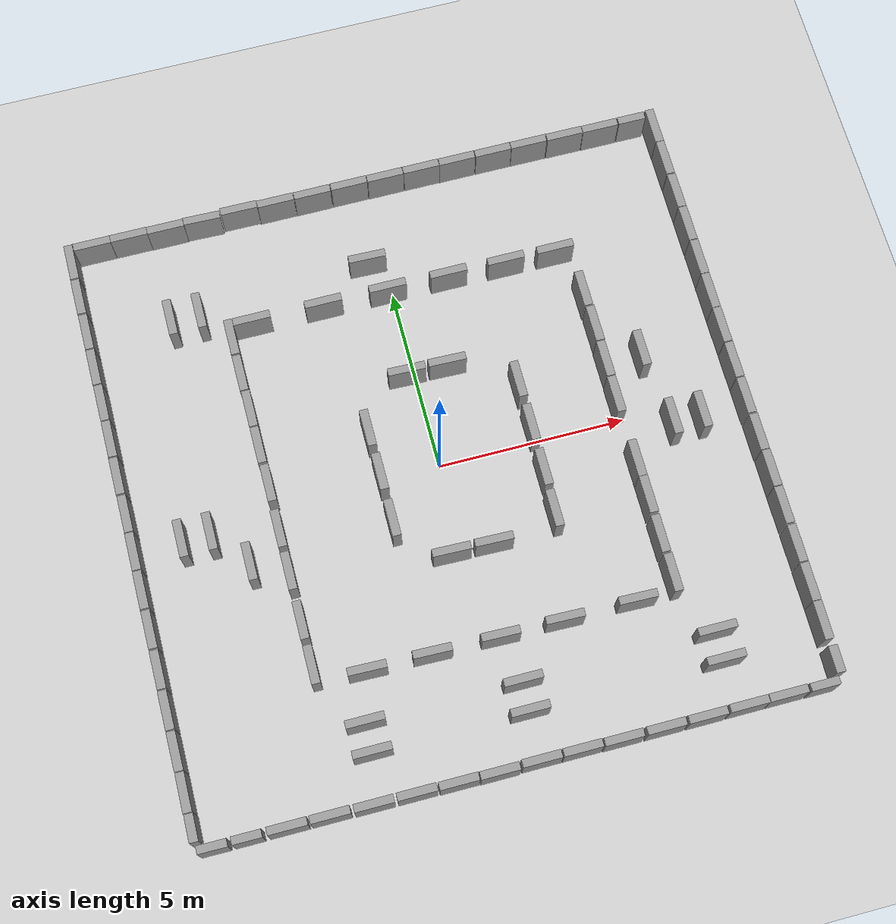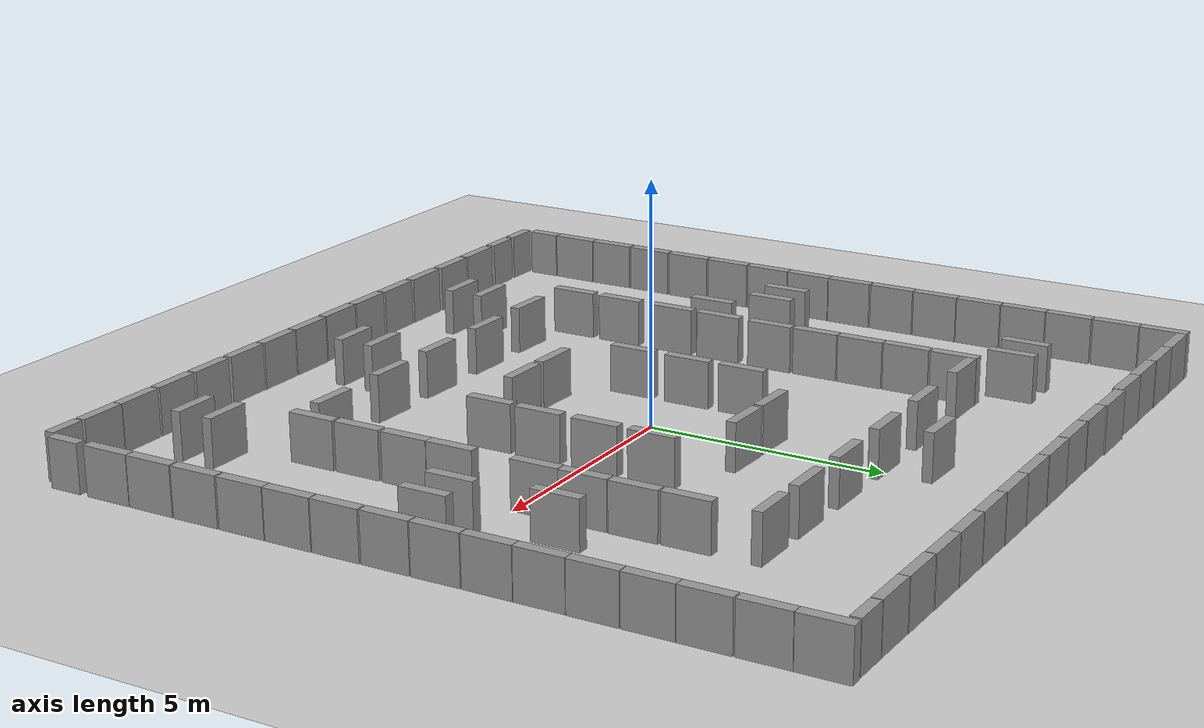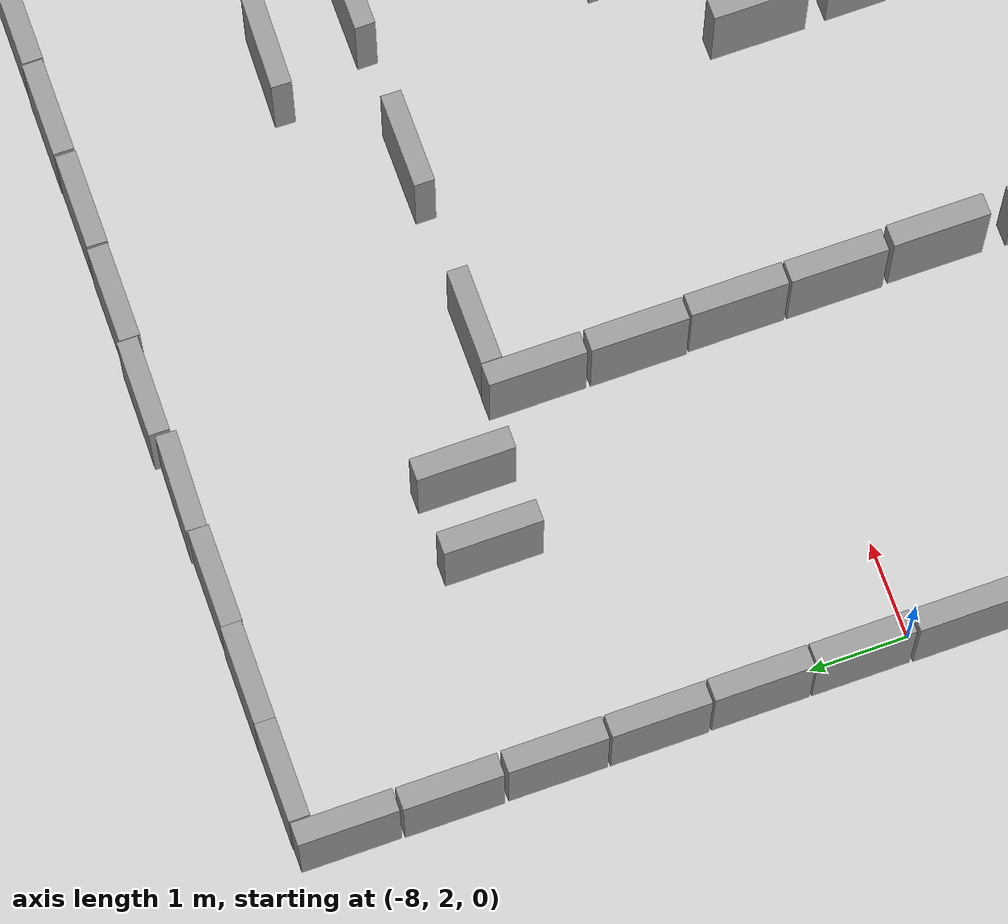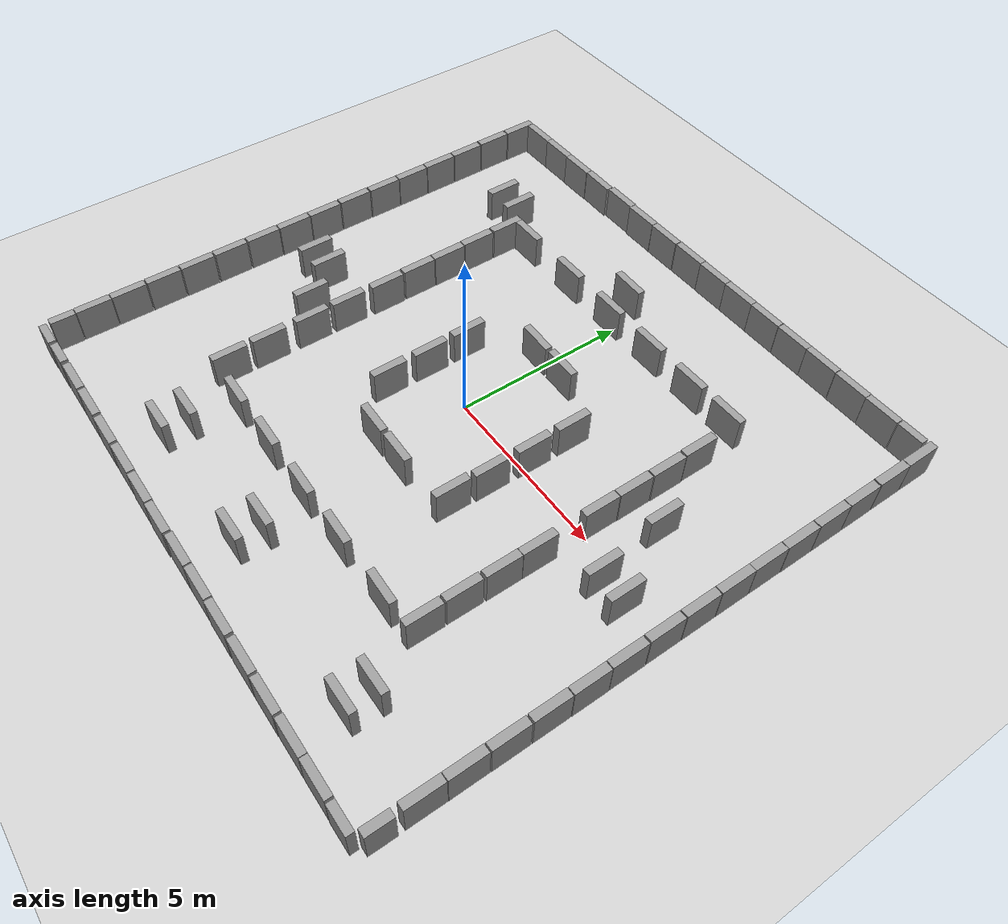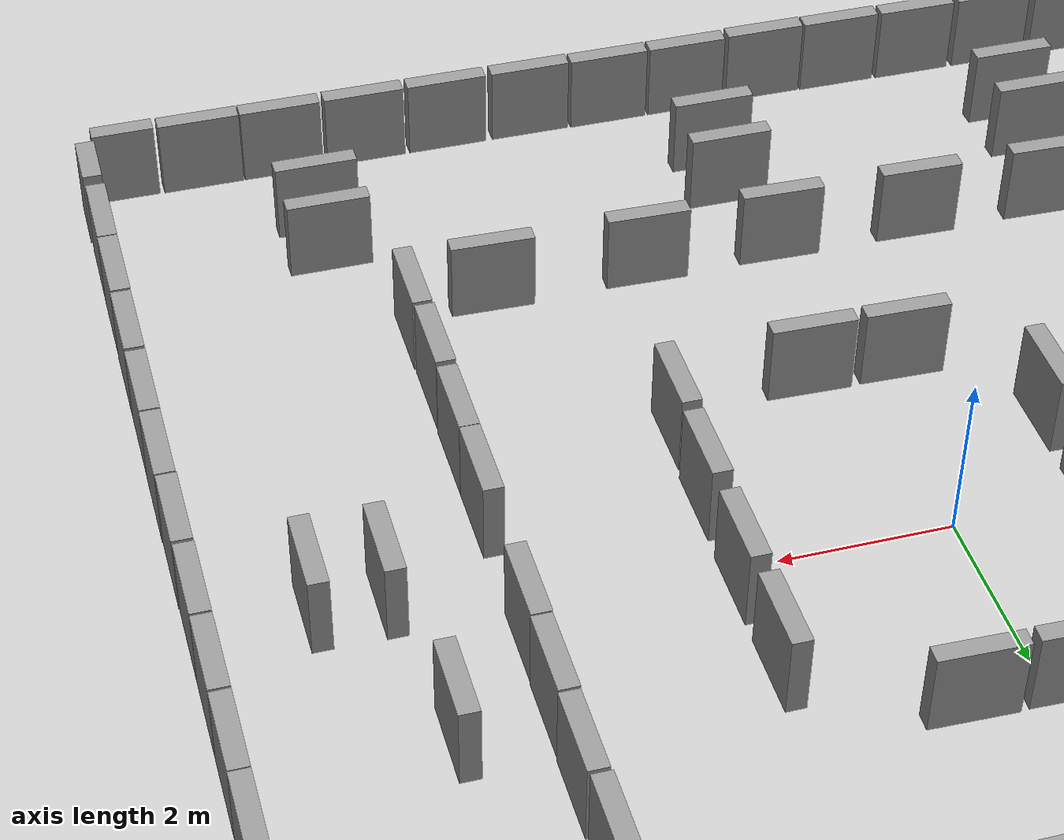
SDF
<sdf version="1.6">
 <world name="default">
  <light name="sun" type="directional">
   <pose>0 0 10 0 -0 0</pose>
   <diffuse>0.8 0.8 0.8 1</diffuse>
   <specular>0.1 0.1 0.1 1</specular>
   <attenuation>
    <range>1000</range>
    <constant>0.9</constant>
    <linear>0.01</linear>
    <quadratic>0.001</quadratic>
   </attenuation>
   <direction>-0.5 0.5 -1</direction>
  </light>
  <model name="ground_plane">
   <static>1</static>
   <static>1</static>
   <link name="link">
    <collision name="collision">
     <geometry><plane><normal>0 0 1</normal><size>100 100</size></plane></geometry>
     <surface><friction><ode><mu>100</mu><mu2>50</mu2></ode></friction></surface>
    </collision>
    <visual name="visual">
     <cast_shadows>0</cast_shadows>
     <geometry><plane><normal>0 0 1</normal><size>100 100</size></plane></geometry>
     <material>
      <script><uri>file://media/materials/scripts/gazebo.material</uri><name>Gazebo/Grey</name></script>
     </material>
    </visual>
   </link>
  </model>
  <gravity>0 0 -9.8</gravity>
  <magnetic_field>6e-06 2.3e-05 -4.2e-05</magnetic_field>
  <atmosphere type="adiabatic"/>
  <physics name="default_physics" default="0" type="ode">
   <max_step_size>0.001</max_step_size>
   <real_time_factor>1</real_time_factor>
   <real_time_update_rate>1000</real_time_update_rate>
  </physics>
  <scene><ambient>0.4 0.4 0.4 1</ambient><background>0.7 0.7 0.7 1</background><shadows>1</shadows></scene>
  <spherical_coordinates>
   <surface_model>EARTH_WGS84</surface_model>
   <latitude_deg>0</latitude_deg>
   <longitude_deg>0</longitude_deg>
   <elevation>0</elevation>
   <heading_deg>0</heading_deg>
  </spherical_coordinates>
  <audio><device>default</device></audio>
  <model name="unit_box_clone">
   <pose>-7.49845 8.12021 0.5 0 -0 0.000459</pose>
   <link name="link">
    <inertial>
     <mass>1</mass>
     <inertia>
      <ixx>0.166667</ixx>
      <ixy>0</ixy>
      <ixz>0</ixz>
      <iyy>0.166667</iyy>
      <iyz>0</iyz>
      <izz>0.166667</izz>
     </inertia>
    </inertial>
    <collision name="collision"><geometry><box><size>1 0.210541 1</size></box></geometry></collision>
    <visual name="visual">
     <geometry><box><size>1 0.210541 1</size></box></geometry>
     <material>
      <script><name>Gazebo/Grey</name><uri>file://media/materials/scripts/gazebo.material</uri></script>
     </material>
    </visual>
   </link>
  </model>
  <model name="unit_box_clone_0">
   <pose>-6.49725 8.11967 0.5 0 -0 -0.00258</pose>
   <link name="link">
    <inertial>
     <mass>1</mass>
     <inertia>
      <ixx>0.166667</ixx>
      <ixy>0</ixy>
      <ixz>0</ixz>
      <iyy>0.166667</iyy>
      <iyz>0</iyz>
      <izz>0.166667</izz>
     </inertia>
    </inertial>
    <collision name="collision"><geometry><box><size>1 0.210541 1</size></box></geometry></collision>
    <visual name="visual">
     <geometry><box><size>1 0.210541 1</size></box></geometry>
     <material>
      <script><name>Gazebo/Grey</name><uri>file://media/materials/scripts/gazebo.material</uri></script>
     </material>
    </visual>
   </link>
  </model>
  <model name="unit_box_clone_1">
   <pose>-5.49726 8.10836 0.499732 -2e-06 -7e-06 -0.002666</pose>
   <link name="link">
    <inertial>
     <mass>1</mass>
     <inertia>
      <ixx>0.166667</ixx>
      <ixy>0</ixy>
      <ixz>0</ixz>
      <iyy>0.166667</iyy>
      <iyz>0</iyz>
      <izz>0.166667</izz>
     </inertia>
    </inertial>
    <collision name="collision"><geometry><box><size>1 0.210541 1</size></box></geometry></collision>
    <visual name="visual">
     <geometry><box><size>1 0.210541 1</size></box></geometry>
     <material>
      <script><name>Gazebo/Grey</name><uri>file://media/materials/scripts/gazebo.material</uri></script>
     </material>
    </visual>
   </link>
  </model>
  <model name="unit_box_clone_2">
   <pose>-4.49488 8.11064 0.499996 -0 2e-06 -0.026421</pose>
   <link name="link">
    <inertial>
     <mass>1</mass>
     <inertia>
      <ixx>0.166667</ixx>
      <ixy>0</ixy>
      <ixz>0</ixz>
      <iyy>0.166667</iyy>
      <iyz>0</iyz>
      <izz>0.166667</izz>
     </inertia>
    </inertial>
    <collision name="collision"><geometry><box><size>1 0.210541 1</size></box></geometry></collision>
    <visual name="visual">
     <geometry><box><size>1 0.210541 1</size></box></geometry>
     <material>
      <script><name>Gazebo/Grey</name><uri>file://media/materials/scripts/gazebo.material</uri></script>
     </material>
    </visual>
   </link>
  </model>
  <model name="unit_box_clone_3">
   <pose>-3.46836 8.15007 0.499999 -1e-06 -2e-06 -0.007855</pose>
   <link name="link">
    <inertial>
     <mass>1</mass>
     <inertia>
      <ixx>0.166667</ixx>
      <ixy>0</ixy>
      <ixz>0</ixz>
      <iyy>0.166667</iyy>
      <iyz>0</iyz>
      <izz>0.166667</izz>
     </inertia>
    </inertial>
    <collision name="collision"><geometry><box><size>1 0.210541 1</size></box></geometry></collision>
    <visual name="visual">
     <geometry><box><size>1 0.210541 1</size></box></geometry>
     <material>
      <script><name>Gazebo/Grey</name><uri>file://media/materials/scripts/gazebo.material</uri></script>
     </material>
    </visual>
   </link>
  </model>
  <model name="unit_box_clone_4">
   <pose>-2.46316 8.1189 0.5 0 -0 0.000459</pose>
   <link name="link">
    <inertial>
     <mass>1</mass>
     <inertia>
      <ixx>0.166667</ixx>
      <ixy>0</ixy>
      <ixz>0</ixz>
      <iyy>0.166667</iyy>
      <iyz>0</iyz>
      <izz>0.166667</izz>
     </inertia>
    </inertial>
    <collision name="collision"><geometry><box><size>1 0.210541 1</size></box></geometry></collision>
    <visual name="visual">
     <geometry><box><size>1 0.210541 1</size></box></geometry>
     <material>
      <script><name>Gazebo/Grey</name><uri>file://media/materials/scripts/gazebo.material</uri></script>
     </material>
    </visual>
   </link>
  </model>
  <model name="unit_box_clone_5">
   <pose>-1.44425 8.11224 0.5 0 -0 0.000459</pose>
   <link name="link">
    <inertial>
     <mass>1</mass>
     <inertia>
      <ixx>0.166667</ixx>
      <ixy>0</ixy>
      <ixz>0</ixz>
      <iyy>0.166667</iyy>
      <iyz>0</iyz>
      <izz>0.166667</izz>
     </inertia>
    </inertial>
    <collision name="collision"><geometry><box><size>1 0.210541 1</size></box></geometry></collision>
    <visual name="visual">
     <geometry><box><size>1 0.210541 1</size></box></geometry>
     <material>
      <script><name>Gazebo/Grey</name><uri>file://media/materials/scripts/gazebo.material</uri></script>
     </material>
    </visual>
   </link>
  </model>
  <model name="unit_box_clone_6">
   <pose>-0.418686 8.11889 0.5 0 -0 0.000459</pose>
   <link name="link">
    <inertial>
     <mass>1</mass>
     <inertia>
      <ixx>0.166667</ixx>
      <ixy>0</ixy>
      <ixz>0</ixz>
      <iyy>0.166667</iyy>
      <iyz>0</iyz>
      <izz>0.166667</izz>
     </inertia>
    </inertial>
    <collision name="collision"><geometry><box><size>1 0.210541 1</size></box></geometry></collision>
    <visual name="visual">
     <geometry><box><size>1 0.210541 1</size></box></geometry>
     <material>
      <script><name>Gazebo/Grey</name><uri>file://media/materials/scripts/gazebo.material</uri></script>
     </material>
    </visual>
   </link>
  </model>
  <model name="unit_box_clone_7">
   <pose>0.592833 8.11176 0.5 0 -0 0.000459</pose>
   <link name="link">
    <inertial>
     <mass>1</mass>
     <inertia>
      <ixx>0.166667</ixx>
      <ixy>0</ixy>
      <ixz>0</ixz>
      <iyy>0.166667</iyy>
      <iyz>0</iyz>
      <izz>0.166667</izz>
     </inertia>
    </inertial>
    <collision name="collision"><geometry><box><size>1 0.210541 1</size></box></geometry></collision>
    <visual name="visual">
     <geometry><box><size>1 0.210541 1</size></box></geometry>
     <material>
      <script><name>Gazebo/Grey</name><uri>file://media/materials/scripts/gazebo.material</uri></script>
     </material>
    </visual>
   </link>
  </model>
  <model name="unit_box_clone_8">
   <pose>1.60043 8.11027 0.5 0 -0 0.000459</pose>
   <link name="link">
    <inertial>
     <mass>1</mass>
     <inertia>
      <ixx>0.166667</ixx>
      <ixy>0</ixy>
      <ixz>0</ixz>
      <iyy>0.166667</iyy>
      <iyz>0</iyz>
      <izz>0.166667</izz>
     </inertia>
    </inertial>
    <collision name="collision"><geometry><box><size>1 0.210541 1</size></box></geometry></collision>
    <visual name="visual">
     <geometry><box><size>1 0.210541 1</size></box></geometry>
     <material>
      <script><name>Gazebo/Grey</name><uri>file://media/materials/scripts/gazebo.material</uri></script>
     </material>
    </visual>
   </link>
  </model>
  <model name="unit_box_clone_9">
   <pose>2.60987 8.10308 0.5 0 -0 0.000459</pose>
   <link name="link">
    <inertial>
     <mass>1</mass>
     <inertia>
      <ixx>0.166667</ixx>
      <ixy>0</ixy>
      <ixz>0</ixz>
      <iyy>0.166667</iyy>
      <iyz>0</iyz>
      <izz>0.166667</izz>
     </inertia>
    </inertial>
    <collision name="collision"><geometry><box><size>1 0.210541 1</size></box></geometry></collision>
    <visual name="visual">
     <geometry><box><size>1 0.210541 1</size></box></geometry>
     <material>
      <script><name>Gazebo/Grey</name><uri>file://media/materials/scripts/gazebo.material</uri></script>
     </material>
    </visual>
   </link>
  </model>
  <model name="unit_box_clone_10">
   <pose>3.62649 8.09949 0.5 0 -0 0.000459</pose>
   <link name="link">
    <inertial>
     <mass>1</mass>
     <inertia>
      <ixx>0.166667</ixx>
      <ixy>0</ixy>
      <ixz>0</ixz>
      <iyy>0.166667</iyy>
      <iyz>0</iyz>
      <izz>0.166667</izz>
     </inertia>
    </inertial>
    <collision name="collision"><geometry><box><size>1 0.210541 1</size></box></geometry></collision>
    <visual name="visual">
     <geometry><box><size>1 0.210541 1</size></box></geometry>
     <material>
      <script><name>Gazebo/Grey</name><uri>file://media/materials/scripts/gazebo.material</uri></script>
     </material>
    </visual>
   </link>
  </model>
  <model name="unit_box_clone_11">
   <pose>4.6331 8.09515 0.499999 1e-06 2e-06 -0.003244</pose>
   <link name="link">
    <inertial>
     <mass>1</mass>
     <inertia>
      <ixx>0.166667</ixx>
      <ixy>0</ixy>
      <ixz>0</ixz>
      <iyy>0.166667</iyy>
      <iyz>0</iyz>
      <izz>0.166667</izz>
     </inertia>
    </inertial>
    <collision name="collision"><geometry><box><size>1 0.210541 1</size></box></geometry></collision>
    <visual name="visual">
     <geometry><box><size>1 0.210541 1</size></box></geometry>
     <material>
      <script><name>Gazebo/Grey</name><uri>file://media/materials/scripts/gazebo.material</uri></script>
     </material>
    </visual>
   </link>
  </model>
  <model name="unit_box_0_clone_0">
   <pose>8.11522 6.68458 0.5 0 0 -0.000278</pose>
   <link name="link">
    <inertial>
     <mass>1</mass>
     <inertia>
      <ixx>0.166667</ixx>
      <ixy>0</ixy>
      <ixz>0</ixz>
      <iyy>0.166667</iyy>
      <iyz>0</iyz>
      <izz>0.166667</izz>
     </inertia>
    </inertial>
    <collision name="collision"><geometry><box><size>0.230819 1 1</size></box></geometry></collision>
    <visual name="visual">
     <geometry><box><size>0.230819 1 1</size></box></geometry>
     <material>
      <script><name>Gazebo/Grey</name><uri>file://media/materials/scripts/gazebo.material</uri></script>
     </material>
    </visual>
   </link>
  </model>
  <model name="unit_box_0_clone_1">
   <pose>8.11915 5.6517 0.5 0 -0 0.000162</pose>
   <link name="link">
    <inertial>
     <mass>1</mass>
     <inertia>
      <ixx>0.166667</ixx>
      <ixy>0</ixy>
      <ixz>0</ixz>
      <iyy>0.166667</iyy>
      <iyz>0</iyz>
      <izz>0.166667</izz>
     </inertia>
    </inertial>
    <collision name="collision"><geometry><box><size>0.230819 1 1</size></box></geometry></collision>
    <visual name="visual">
     <geometry><box><size>0.230819 1 1</size></box></geometry>
     <material>
      <script><name>Gazebo/Grey</name><uri>file://media/materials/scripts/gazebo.material</uri></script>
     </material>
    </visual>
   </link>
  </model>
  <model name="unit_box_0_clone_2">
   <pose>8.11914 4.64016 0.5 0 -0 0.000256</pose>
   <link name="link">
    <inertial>
     <mass>1</mass>
     <inertia>
      <ixx>0.166667</ixx>
      <ixy>0</ixy>
      <ixz>0</ixz>
      <iyy>0.166667</iyy>
      <iyz>0</iyz>
      <izz>0.166667</izz>
     </inertia>
    </inertial>
    <collision name="collision"><geometry><box><size>0.230819 1 1</size></box></geometry></collision>
    <visual name="visual">
     <geometry><box><size>0.230819 1 1</size></box></geometry>
     <material>
      <script><name>Gazebo/Grey</name><uri>file://media/materials/scripts/gazebo.material</uri></script>
     </material>
    </visual>
   </link>
  </model>
  <model name="unit_box_0_clone_3">
   <pose>8.11914 3.62228 0.5 0 -0 0.000237</pose>
   <link name="link">
    <inertial>
     <mass>1</mass>
     <inertia>
      <ixx>0.166667</ixx>
      <ixy>0</ixy>
      <ixz>0</ixz>
      <iyy>0.166667</iyy>
      <iyz>0</iyz>
      <izz>0.166667</izz>
     </inertia>
    </inertial>
    <collision name="collision"><geometry><box><size>0.230819 1 1</size></box></geometry></collision>
    <visual name="visual">
     <geometry><box><size>0.230819 1 1</size></box></geometry>
     <material>
      <script><name>Gazebo/Grey</name><uri>file://media/materials/scripts/gazebo.material</uri></script>
     </material>
    </visual>
   </link>
  </model>
  <model name="unit_box_0_clone_4">
   <pose>8.11332 2.61063 0.5 0 -0 -0.000997</pose>
   <link name="link">
    <inertial>
     <mass>1</mass>
     <inertia>
      <ixx>0.166667</ixx>
      <ixy>0</ixy>
      <ixz>0</ixz>
      <iyy>0.166667</iyy>
      <iyz>0</iyz>
      <izz>0.166667</izz>
     </inertia>
    </inertial>
    <collision name="collision"><geometry><box><size>0.230819 1 1</size></box></geometry></collision>
    <visual name="visual">
     <geometry><box><size>0.230819 1 1</size></box></geometry>
     <material>
      <script><name>Gazebo/Grey</name><uri>file://media/materials/scripts/gazebo.material</uri></script>
     </material>
    </visual>
   </link>
  </model>
  <model name="unit_box_0_clone_5">
   <pose>8.11277 1.59919 0.5 0 -0 0.000237</pose>
   <link name="link">
    <inertial>
     <mass>1</mass>
     <inertia>
      <ixx>0.166667</ixx>
      <ixy>0</ixy>
      <ixz>0</ixz>
      <iyy>0.166667</iyy>
      <iyz>0</iyz>
      <izz>0.166667</izz>
     </inertia>
    </inertial>
    <collision name="collision"><geometry><box><size>0.230819 1 1</size></box></geometry></collision>
    <visual name="visual">
     <geometry><box><size>0.230819 1 1</size></box></geometry>
     <material>
      <script><name>Gazebo/Grey</name><uri>file://media/materials/scripts/gazebo.material</uri></script>
     </material>
    </visual>
   </link>
  </model>
  <model name="unit_box_0_clone_6">
   <pose>8.11277 0.574937 0.5 0 -0 0.000237</pose>
   <link name="link">
    <inertial>
     <mass>1</mass>
     <inertia>
      <ixx>0.166667</ixx>
      <ixy>0</ixy>
      <ixz>0</ixz>
      <iyy>0.166667</iyy>
      <iyz>0</iyz>
      <izz>0.166667</izz>
     </inertia>
    </inertial>
    <collision name="collision"><geometry><box><size>0.230819 1 1</size></box></geometry></collision>
    <visual name="visual">
     <geometry><box><size>0.230819 1 1</size></box></geometry>
     <material>
      <script><name>Gazebo/Grey</name><uri>file://media/materials/scripts/gazebo.material</uri></script>
     </material>
    </visual>
   </link>
  </model>
  <model name="unit_box_0_clone_7">
   <pose>8.11276 -0.449321 0.5 0 -0 0.000237</pose>
   <link name="link">
    <inertial>
     <mass>1</mass>
     <inertia>
      <ixx>0.166667</ixx>
      <ixy>0</ixy>
      <ixz>0</ixz>
      <iyy>0.166667</iyy>
      <iyz>0</iyz>
      <izz>0.166667</izz>
     </inertia>
    </inertial>
    <collision name="collision"><geometry><box><size>0.230819 1 1</size></box></geometry></collision>
    <visual name="visual">
     <geometry><box><size>0.230819 1 1</size></box></geometry>
     <material>
      <script><name>Gazebo/Grey</name><uri>file://media/materials/scripts/gazebo.material</uri></script>
     </material>
    </visual>
   </link>
  </model>
  <model name="unit_box_0_clone_8">
   <pose>8.11912 -1.48629 0.5 0 -0 0.000237</pose>
   <link name="link">
    <inertial>
     <mass>1</mass>
     <inertia>
      <ixx>0.166667</ixx>
      <ixy>0</ixy>
      <ixz>0</ixz>
      <iyy>0.166667</iyy>
      <iyz>0</iyz>
      <izz>0.166667</izz>
     </inertia>
    </inertial>
    <collision name="collision"><geometry><box><size>0.230819 1 1</size></box></geometry></collision>
    <visual name="visual">
     <geometry><box><size>0.230819 1 1</size></box></geometry>
     <material>
      <script><name>Gazebo/Grey</name><uri>file://media/materials/scripts/gazebo.material</uri></script>
     </material>
    </visual>
   </link>
  </model>
  <model name="unit_box_0_clone_9">
   <pose>8.12548 -2.5042 0.5 0 -0 0.000237</pose>
   <link name="link">
    <inertial>
     <mass>1</mass>
     <inertia>
      <ixx>0.166667</ixx>
      <ixy>0</ixy>
      <ixz>0</ixz>
      <iyy>0.166667</iyy>
      <iyz>0</iyz>
      <izz>0.166667</izz>
     </inertia>
    </inertial>
    <collision name="collision"><geometry><box><size>0.230819 1 1</size></box></geometry></collision>
    <visual name="visual">
     <geometry><box><size>0.230819 1 1</size></box></geometry>
     <material>
      <script><name>Gazebo/Grey</name><uri>file://media/materials/scripts/gazebo.material</uri></script>
     </material>
    </visual>
   </link>
  </model>
  <model name="unit_box_0_clone_10">
   <pose>8.12331 -3.52223 0.5 0 -0 0.000237</pose>
   <link name="link">
    <inertial>
     <mass>1</mass>
     <inertia>
      <ixx>0.166667</ixx>
      <ixy>0</ixy>
      <ixz>0</ixz>
      <iyy>0.166667</iyy>
      <iyz>0</iyz>
      <izz>0.166667</izz>
     </inertia>
    </inertial>
    <collision name="collision"><geometry><box><size>0.230819 1 1</size></box></geometry></collision>
    <visual name="visual">
     <geometry><box><size>0.230819 1 1</size></box></geometry>
     <material>
      <script><name>Gazebo/Grey</name><uri>file://media/materials/scripts/gazebo.material</uri></script>
     </material>
    </visual>
   </link>
  </model>
  <model name="unit_box_0_clone_11">
   <pose>8.1233 -4.56316 0.5 0 -0 0.000237</pose>
   <link name="link">
    <inertial>
     <mass>1</mass>
     <inertia>
      <ixx>0.166667</ixx>
      <ixy>0</ixy>
      <ixz>0</ixz>
      <iyy>0.166667</iyy>
      <iyz>0</iyz>
      <izz>0.166667</izz>
     </inertia>
    </inertial>
    <collision name="collision"><geometry><box><size>0.230819 1 1</size></box></geometry></collision>
    <visual name="visual">
     <geometry><box><size>0.230819 1 1</size></box></geometry>
     <material>
      <script><name>Gazebo/Grey</name><uri>file://media/materials/scripts/gazebo.material</uri></script>
     </material>
    </visual>
   </link>
  </model>
  <model name="unit_box_0_clone_12">
   <pose>8.11815 -5.59377 0.5 0 -0 0.000237</pose>
   <link name="link">
    <inertial>
     <mass>1</mass>
     <inertia>
      <ixx>0.166667</ixx>
      <ixy>0</ixy>
      <ixz>0</ixz>
      <iyy>0.166667</iyy>
      <iyz>0</iyz>
      <izz>0.166667</izz>
     </inertia>
    </inertial>
    <collision name="collision"><geometry><box><size>0.230819 1 1</size></box></geometry></collision>
    <visual name="visual">
     <geometry><box><size>0.230819 1 1</size></box></geometry>
     <material>
      <script><name>Gazebo/Grey</name><uri>file://media/materials/scripts/gazebo.material</uri></script>
     </material>
    </visual>
   </link>
  </model>
  <model name="unit_box_0_clone_13">
   <pose>8.11333 -6.60776 0.5 0 -0 -0.005418</pose>
   <link name="link">
    <inertial>
     <mass>1</mass>
     <inertia>
      <ixx>0.166667</ixx>
      <ixy>0</ixy>
      <ixz>0</ixz>
      <iyy>0.166667</iyy>
      <iyz>0</iyz>
      <izz>0.166667</izz>
     </inertia>
    </inertial>
    <collision name="collision"><geometry><box><size>0.230819 1 1</size></box></geometry></collision>
    <visual name="visual">
     <geometry><box><size>0.230819 1 1</size></box></geometry>
     <material>
      <script><name>Gazebo/Grey</name><uri>file://media/materials/scripts/gazebo.material</uri></script>
     </material>
    </visual>
   </link>
  </model>
  <model name="unit_box_clone_15_clone_0">
   <pose>6.71207 -8.13083 0.5 0 -0 0.000459</pose>
   <link name="link">
    <inertial>
     <mass>1</mass>
     <inertia>
      <ixx>0.166667</ixx>
      <ixy>0</ixy>
      <ixz>0</ixz>
      <iyy>0.166667</iyy>
      <iyz>0</iyz>
      <izz>0.166667</izz>
     </inertia>
    </inertial>
    <collision name="collision"><geometry><box><size>1 0.210541 1</size></box></geometry></collision>
    <visual name="visual">
     <geometry><box><size>1 0.210541 1</size></box></geometry>
     <material>
      <script><name>Gazebo/Grey</name><uri>file://media/materials/scripts/gazebo.material</uri></script>
     </material>
    </visual>
   </link>
  </model>
  <model name="unit_box_clone_15_clone_1">
   <pose>5.69715 -8.13082 0.5 0 -0 0.000459</pose>
   <link name="link">
    <inertial>
     <mass>1</mass>
     <inertia>
      <ixx>0.166667</ixx>
      <ixy>0</ixy>
      <ixz>0</ixz>
      <iyy>0.166667</iyy>
      <iyz>0</iyz>
      <izz>0.166667</izz>
     </inertia>
    </inertial>
    <collision name="collision"><geometry><box><size>1 0.210541 1</size></box></geometry></collision>
    <visual name="visual">
     <geometry><box><size>1 0.210541 1</size></box></geometry>
     <material>
      <script><name>Gazebo/Grey</name><uri>file://media/materials/scripts/gazebo.material</uri></script>
     </material>
    </visual>
   </link>
  </model>
  <model name="unit_box_clone_15_clone_2">
   <pose>4.63881 -8.137 0.5 0 -0 0.000459</pose>
   <link name="link">
    <inertial>
     <mass>1</mass>
     <inertia>
      <ixx>0.166667</ixx>
      <ixy>0</ixy>
      <ixz>0</ixz>
      <iyy>0.166667</iyy>
      <iyz>0</iyz>
      <izz>0.166667</izz>
     </inertia>
    </inertial>
    <collision name="collision"><geometry><box><size>1 0.210541 1</size></box></geometry></collision>
    <visual name="visual">
     <geometry><box><size>1 0.210541 1</size></box></geometry>
     <material>
      <script><name>Gazebo/Grey</name><uri>file://media/materials/scripts/gazebo.material</uri></script>
     </material>
    </visual>
   </link>
  </model>
  <model name="unit_box_clone_15_clone_3">
   <pose>3.57975 -8.137 0.5 0 -0 0.000459</pose>
   <link name="link">
    <inertial>
     <mass>1</mass>
     <inertia>
      <ixx>0.166667</ixx>
      <ixy>0</ixy>
      <ixz>0</ixz>
      <iyy>0.166667</iyy>
      <iyz>0</iyz>
      <izz>0.166667</izz>
     </inertia>
    </inertial>
    <collision name="collision"><geometry><box><size>1 0.210541 1</size></box></geometry></collision>
    <visual name="visual">
     <geometry><box><size>1 0.210541 1</size></box></geometry>
     <material>
      <script><name>Gazebo/Grey</name><uri>file://media/materials/scripts/gazebo.material</uri></script>
     </material>
    </visual>
   </link>
  </model>
  <model name="unit_box_clone_15_clone_4">
   <pose>2.49815 -8.13699 0.5 0 -0 0.000459</pose>
   <link name="link">
    <inertial>
     <mass>1</mass>
     <inertia>
      <ixx>0.166667</ixx>
      <ixy>0</ixy>
      <ixz>0</ixz>
      <iyy>0.166667</iyy>
      <iyz>0</iyz>
      <izz>0.166667</izz>
     </inertia>
    </inertial>
    <collision name="collision"><geometry><box><size>1 0.210541 1</size></box></geometry></collision>
    <visual name="visual">
     <geometry><box><size>1 0.210541 1</size></box></geometry>
     <material>
      <script><name>Gazebo/Grey</name><uri>file://media/materials/scripts/gazebo.material</uri></script>
     </material>
    </visual>
   </link>
  </model>
  <model name="unit_box_clone_15_clone_5">
   <pose>1.46162 -8.12572 0.5 0 -0 0.000459</pose>
   <link name="link">
    <inertial>
     <mass>1</mass>
     <inertia>
      <ixx>0.166667</ixx>
      <ixy>0</ixy>
      <ixz>0</ixz>
      <iyy>0.166667</iyy>
      <iyz>0</iyz>
      <izz>0.166667</izz>
     </inertia>
    </inertial>
    <collision name="collision"><geometry><box><size>1 0.210541 1</size></box></geometry></collision>
    <visual name="visual">
     <geometry><box><size>1 0.210541 1</size></box></geometry>
     <material>
      <script><name>Gazebo/Grey</name><uri>file://media/materials/scripts/gazebo.material</uri></script>
     </material>
    </visual>
   </link>
  </model>
  <model name="unit_box_clone_15_clone_6">
   <pose>0.425086 -8.12571 0.5 0 -0 0.000459</pose>
   <link name="link">
    <inertial>
     <mass>1</mass>
     <inertia>
      <ixx>0.166667</ixx>
      <ixy>0</ixy>
      <ixz>0</ixz>
      <iyy>0.166667</iyy>
      <iyz>0</iyz>
      <izz>0.166667</izz>
     </inertia>
    </inertial>
    <collision name="collision"><geometry><box><size>1 0.210541 1</size></box></geometry></collision>
    <visual name="visual">
     <geometry><box><size>1 0.210541 1</size></box></geometry>
     <material>
      <script><name>Gazebo/Grey</name><uri>file://media/materials/scripts/gazebo.material</uri></script>
     </material>
    </visual>
   </link>
  </model>
  <model name="unit_box_clone_15_clone_7">
   <pose>-0.633976 -8.14826 0.5 0 -0 0.000459</pose>
   <link name="link">
    <inertial>
     <mass>1</mass>
     <inertia>
      <ixx>0.166667</ixx>
      <ixy>0</ixy>
      <ixz>0</ixz>
      <iyy>0.166667</iyy>
      <iyz>0</iyz>
      <izz>0.166667</izz>
     </inertia>
    </inertial>
    <collision name="collision"><geometry><box><size>1 0.210541 1</size></box></geometry></collision>
    <visual name="visual">
     <geometry><box><size>1 0.210541 1</size></box></geometry>
     <material>
      <script><name>Gazebo/Grey</name><uri>file://media/materials/scripts/gazebo.material</uri></script>
     </material>
    </visual>
   </link>
  </model>
  <model name="unit_box_clone_15_clone_8">
   <pose>-1.65923 -8.13698 0.5 0 -0 0.000459</pose>
   <link name="link">
    <inertial>
     <mass>1</mass>
     <inertia>
      <ixx>0.166667</ixx>
      <ixy>0</ixy>
      <ixz>0</ixz>
      <iyy>0.166667</iyy>
      <iyz>0</iyz>
      <izz>0.166667</izz>
     </inertia>
    </inertial>
    <collision name="collision"><geometry><box><size>1 0.210541 1</size></box></geometry></collision>
    <visual name="visual">
     <geometry><box><size>1 0.210541 1</size></box></geometry>
     <material>
      <script><name>Gazebo/Grey</name><uri>file://media/materials/scripts/gazebo.material</uri></script>
     </material>
    </visual>
   </link>
  </model>
  <model name="unit_box_clone_15_clone_9">
   <pose>-2.70703 -8.12573 0.5 0 -0 0.000459</pose>
   <link name="link">
    <inertial>
     <mass>1</mass>
     <inertia>
      <ixx>0.166667</ixx>
      <ixy>0</ixy>
      <ixz>0</ixz>
      <iyy>0.166667</iyy>
      <iyz>0</iyz>
      <izz>0.166667</izz>
     </inertia>
    </inertial>
    <collision name="collision"><geometry><box><size>1 0.210541 1</size></box></geometry></collision>
    <visual name="visual">
     <geometry><box><size>1 0.210541 1</size></box></geometry>
     <material>
      <script><name>Gazebo/Grey</name><uri>file://media/materials/scripts/gazebo.material</uri></script>
     </material>
    </visual>
   </link>
  </model>
  <model name="unit_box_clone_15_clone_10">
   <pose>-3.77736 -8.12572 0.5 0 -0 0.000459</pose>
   <link name="link">
    <inertial>
     <mass>1</mass>
     <inertia>
      <ixx>0.166667</ixx>
      <ixy>0</ixy>
      <ixz>0</ixz>
      <iyy>0.166667</iyy>
      <iyz>0</iyz>
      <izz>0.166667</izz>
     </inertia>
    </inertial>
    <collision name="collision"><geometry><box><size>1 0.210541 1</size></box></geometry></collision>
    <visual name="visual">
     <geometry><box><size>1 0.210541 1</size></box></geometry>
     <material>
      <script><name>Gazebo/Grey</name><uri>file://media/materials/scripts/gazebo.material</uri></script>
     </material>
    </visual>
   </link>
  </model>
  <model name="unit_box_clone_15_clone_11">
   <pose>-4.85896 -8.11446 0.5 0 -0 0.000459</pose>
   <link name="link">
    <inertial>
     <mass>1</mass>
     <inertia>
      <ixx>0.166667</ixx>
      <ixy>0</ixy>
      <ixz>0</ixz>
      <iyy>0.166667</iyy>
      <iyz>0</iyz>
      <izz>0.166667</izz>
     </inertia>
    </inertial>
    <collision name="collision"><geometry><box><size>1 0.210541 1</size></box></geometry></collision>
    <visual name="visual">
     <geometry><box><size>1 0.210541 1</size></box></geometry>
     <material>
      <script><name>Gazebo/Grey</name><uri>file://media/materials/scripts/gazebo.material</uri></script>
     </material>
    </visual>
   </link>
  </model>
  <model name="unit_box_clone_15_clone_12">
   <pose>-5.91802 -8.11445 0.5 0 -0 0.000459</pose>
   <link name="link">
    <inertial>
     <mass>1</mass>
     <inertia>
      <ixx>0.166667</ixx>
      <ixy>0</ixy>
      <ixz>0</ixz>
      <iyy>0.166667</iyy>
      <iyz>0</iyz>
      <izz>0.166667</izz>
     </inertia>
    </inertial>
    <collision name="collision"><geometry><box><size>1 0.210541 1</size></box></geometry></collision>
    <visual name="visual">
     <geometry><box><size>1 0.210541 1</size></box></geometry>
     <material>
      <script><name>Gazebo/Grey</name><uri>file://media/materials/scripts/gazebo.material</uri></script>
     </material>
    </visual>
   </link>
  </model>
  <model name="unit_box_0_clone_4_clone">
   <pose>-8.12647 7.71769 0.5 0 -0 0.000237</pose>
   <link name="link">
    <inertial>
     <mass>1</mass>
     <inertia>
      <ixx>0.166667</ixx>
      <ixy>0</ixy>
      <ixz>0</ixz>
      <iyy>0.166667</iyy>
      <iyz>0</iyz>
      <izz>0.166667</izz>
     </inertia>
    </inertial>
    <collision name="collision"><geometry><box><size>0.230819 1 1</size></box></geometry></collision>
    <visual name="visual">
     <geometry><box><size>0.230819 1 1</size></box></geometry>
     <material>
      <script><name>Gazebo/Grey</name><uri>file://media/materials/scripts/gazebo.material</uri></script>
     </material>
    </visual>
   </link>
  </model>
  <model name="unit_box_0_clone_4_clone_0">
   <pose>-8.13281 6.68715 0.5 0 -0 0.000237</pose>
   <link name="link">
    <inertial>
     <mass>1</mass>
     <inertia>
      <ixx>0.166667</ixx>
      <ixy>0</ixy>
      <ixz>0</ixz>
      <iyy>0.166667</iyy>
      <iyz>0</iyz>
      <izz>0.166667</izz>
     </inertia>
    </inertial>
    <collision name="collision"><geometry><box><size>0.230819 1 1</size></box></geometry></collision>
    <visual name="visual">
     <geometry><box><size>0.230819 1 1</size></box></geometry>
     <material>
      <script><name>Gazebo/Grey</name><uri>file://media/materials/scripts/gazebo.material</uri></script>
     </material>
    </visual>
   </link>
  </model>
  <model name="unit_box_0_clone_4_clone_1">
   <pose>-8.12606 5.64722 0.5 0 -0 0.000237</pose>
   <link name="link">
    <inertial>
     <mass>1</mass>
     <inertia>
      <ixx>0.166667</ixx>
      <ixy>0</ixy>
      <ixz>0</ixz>
      <iyy>0.166667</iyy>
      <iyz>0</iyz>
      <izz>0.166667</izz>
     </inertia>
    </inertial>
    <collision name="collision"><geometry><box><size>0.230819 1 1</size></box></geometry></collision>
    <visual name="visual">
     <geometry><box><size>0.230819 1 1</size></box></geometry>
     <material>
      <script><name>Gazebo/Grey</name><uri>file://media/materials/scripts/gazebo.material</uri></script>
     </material>
    </visual>
   </link>
  </model>
  <model name="unit_box_0_clone_4_clone_2">
   <pose>-8.12607 4.6208 0.5 0 -0 0.000237</pose>
   <link name="link">
    <inertial>
     <mass>1</mass>
     <inertia>
      <ixx>0.166667</ixx>
      <ixy>0</ixy>
      <ixz>0</ixz>
      <iyy>0.166667</iyy>
      <iyz>0</iyz>
      <izz>0.166667</izz>
     </inertia>
    </inertial>
    <collision name="collision"><geometry><box><size>0.230819 1 1</size></box></geometry></collision>
    <visual name="visual">
     <geometry><box><size>0.230819 1 1</size></box></geometry>
     <material>
      <script><name>Gazebo/Grey</name><uri>file://media/materials/scripts/gazebo.material</uri></script>
     </material>
    </visual>
   </link>
  </model>
  <model name="unit_box_0_clone_4_clone_3">
   <pose>-8.11932 3.59437 0.5 0 -0 0.000237</pose>
   <link name="link">
    <inertial>
     <mass>1</mass>
     <inertia>
      <ixx>0.166667</ixx>
      <ixy>0</ixy>
      <ixz>0</ixz>
      <iyy>0.166667</iyy>
      <iyz>0</iyz>
      <izz>0.166667</izz>
     </inertia>
    </inertial>
    <collision name="collision"><geometry><box><size>0.230819 1 1</size></box></geometry></collision>
    <visual name="visual">
     <geometry><box><size>0.230819 1 1</size></box></geometry>
     <material>
      <script><name>Gazebo/Grey</name><uri>file://media/materials/scripts/gazebo.material</uri></script>
     </material>
    </visual>
   </link>
  </model>
  <model name="unit_box_0_clone_4_clone_4">
   <pose>-8.11932 2.57471 0.5 0 -0 0.000237</pose>
   <link name="link">
    <inertial>
     <mass>1</mass>
     <inertia>
      <ixx>0.166667</ixx>
      <ixy>0</ixy>
      <ixz>0</ixz>
      <iyy>0.166667</iyy>
      <iyz>0</iyz>
      <izz>0.166667</izz>
     </inertia>
    </inertial>
    <collision name="collision"><geometry><box><size>0.230819 1 1</size></box></geometry></collision>
    <visual name="visual">
     <geometry><box><size>0.230819 1 1</size></box></geometry>
     <material>
      <script><name>Gazebo/Grey</name><uri>file://media/materials/scripts/gazebo.material</uri></script>
     </material>
    </visual>
   </link>
  </model>
  <model name="unit_box_0_clone_4_clone_5">
   <pose>-8.12608 1.54157 0.5 0 -0 0.000237</pose>
   <link name="link">
    <inertial>
     <mass>1</mass>
     <inertia>
      <ixx>0.166667</ixx>
      <ixy>0</ixy>
      <ixz>0</ixz>
      <iyy>0.166667</iyy>
      <iyz>0</iyz>
      <izz>0.166667</izz>
     </inertia>
    </inertial>
    <collision name="collision"><geometry><box><size>0.230819 1 1</size></box></geometry></collision>
    <visual name="visual">
     <geometry><box><size>0.230819 1 1</size></box></geometry>
     <material>
      <script><name>Gazebo/Grey</name><uri>file://media/materials/scripts/gazebo.material</uri></script>
     </material>
    </visual>
   </link>
  </model>
  <model name="unit_box_0_clone_4_clone_6">
   <pose>-8.11933 0.501629 0.5 0 -0 0.000237</pose>
   <link name="link">
    <inertial>
     <mass>1</mass>
     <inertia>
      <ixx>0.166667</ixx>
      <ixy>0</ixy>
      <ixz>0</ixz>
      <iyy>0.166667</iyy>
      <iyz>0</iyz>
      <izz>0.166667</izz>
     </inertia>
    </inertial>
    <collision name="collision"><geometry><box><size>0.230819 1 1</size></box></geometry></collision>
    <visual name="visual">
     <geometry><box><size>0.230819 1 1</size></box></geometry>
     <material>
      <script><name>Gazebo/Grey</name><uri>file://media/materials/scripts/gazebo.material</uri></script>
     </material>
    </visual>
   </link>
  </model>
  <model name="unit_box_0_clone_4_clone_7">
   <pose>-8.12609 -0.518035 0.5 0 -0 0.000237</pose>
   <link name="link">
    <inertial>
     <mass>1</mass>
     <inertia>
      <ixx>0.166667</ixx>
      <ixy>0</ixy>
      <ixz>0</ixz>
      <iyy>0.166667</iyy>
      <iyz>0</iyz>
      <izz>0.166667</izz>
     </inertia>
    </inertial>
    <collision name="collision"><geometry><box><size>0.230819 1 1</size></box></geometry></collision>
    <visual name="visual">
     <geometry><box><size>0.230819 1 1</size></box></geometry>
     <material>
      <script><name>Gazebo/Grey</name><uri>file://media/materials/scripts/gazebo.material</uri></script>
     </material>
    </visual>
   </link>
  </model>
  <model name="unit_box_0_clone_4_clone_8">
   <pose>-8.13284 -1.54445 0.5 0 -0 0.000237</pose>
   <link name="link">
    <inertial>
     <mass>1</mass>
     <inertia>
      <ixx>0.166667</ixx>
      <ixy>0</ixy>
      <ixz>0</ixz>
      <iyy>0.166667</iyy>
      <iyz>0</iyz>
      <izz>0.166667</izz>
     </inertia>
    </inertial>
    <collision name="collision"><geometry><box><size>0.230819 1 1</size></box></geometry></collision>
    <visual name="visual">
     <geometry><box><size>0.230819 1 1</size></box></geometry>
     <material>
      <script><name>Gazebo/Grey</name><uri>file://media/materials/scripts/gazebo.material</uri></script>
     </material>
    </visual>
   </link>
  </model>
  <model name="unit_box_0_clone_4_clone_9">
   <pose>-8.13285 -2.58439 0.5 0 -0 0.000237</pose>
   <link name="link">
    <inertial>
     <mass>1</mass>
     <inertia>
      <ixx>0.166667</ixx>
      <ixy>0</ixy>
      <ixz>0</ixz>
      <iyy>0.166667</iyy>
      <iyz>0</iyz>
      <izz>0.166667</izz>
     </inertia>
    </inertial>
    <collision name="collision"><geometry><box><size>0.230819 1 1</size></box></geometry></collision>
    <visual name="visual">
     <geometry><box><size>0.230819 1 1</size></box></geometry>
     <material>
      <script><name>Gazebo/Grey</name><uri>file://media/materials/scripts/gazebo.material</uri></script>
     </material>
    </visual>
   </link>
  </model>
  <model name="unit_box_0_clone_4_clone_10">
   <pose>-8.13285 -3.62431 0.5 0 -0 0.000237</pose>
   <link name="link">
    <inertial>
     <mass>1</mass>
     <inertia>
      <ixx>0.166667</ixx>
      <ixy>0</ixy>
      <ixz>0</ixz>
      <iyy>0.166667</iyy>
      <iyz>0</iyz>
      <izz>0.166667</izz>
     </inertia>
    </inertial>
    <collision name="collision"><geometry><box><size>0.230819 1 1</size></box></geometry></collision>
    <visual name="visual">
     <geometry><box><size>0.230819 1 1</size></box></geometry>
     <material>
      <script><name>Gazebo/Grey</name><uri>file://media/materials/scripts/gazebo.material</uri></script>
     </material>
    </visual>
   </link>
  </model>
  <model name="unit_box_0_clone_4_clone_11">
   <pose>-8.1396 -4.65747 0.5 0 -0 0.000237</pose>
   <link name="link">
    <inertial>
     <mass>1</mass>
     <inertia>
      <ixx>0.166667</ixx>
      <ixy>0</ixy>
      <ixz>0</ixz>
      <iyy>0.166667</iyy>
      <iyz>0</iyz>
      <izz>0.166667</izz>
     </inertia>
    </inertial>
    <collision name="collision"><geometry><box><size>0.230819 1 1</size></box></geometry></collision>
    <visual name="visual">
     <geometry><box><size>0.230819 1 1</size></box></geometry>
     <material>
      <script><name>Gazebo/Grey</name><uri>file://media/materials/scripts/gazebo.material</uri></script>
     </material>
    </visual>
   </link>
  </model>
  <model name="unit_box_0_clone_4_clone_12">
   <pose>-8.1396 -5.69064 0.5 0 -0 0.000237</pose>
   <link name="link">
    <inertial>
     <mass>1</mass>
     <inertia>
      <ixx>0.166667</ixx>
      <ixy>0</ixy>
      <ixz>0</ixz>
      <iyy>0.166667</iyy>
      <iyz>0</iyz>
      <izz>0.166667</izz>
     </inertia>
    </inertial>
    <collision name="collision"><geometry><box><size>0.230819 1 1</size></box></geometry></collision>
    <visual name="visual">
     <geometry><box><size>0.230819 1 1</size></box></geometry>
     <material>
      <script><name>Gazebo/Grey</name><uri>file://media/materials/scripts/gazebo.material</uri></script>
     </material>
    </visual>
   </link>
  </model>
  <model name="unit_box_0_clone_4_clone_13">
   <pose>-8.14113 -6.70873 0.5 0 -0 -0.008646</pose>
   <link name="link">
    <inertial>
     <mass>1</mass>
     <inertia>
      <ixx>0.166667</ixx>
      <ixy>0</ixy>
      <ixz>0</ixz>
      <iyy>0.166667</iyy>
      <iyz>0</iyz>
      <izz>0.166667</izz>
     </inertia>
    </inertial>
    <collision name="collision"><geometry><box><size>0.230819 1 1</size></box></geometry></collision>
    <visual name="visual">
     <geometry><box><size>0.230819 1 1</size></box></geometry>
     <material>
      <script><name>Gazebo/Grey</name><uri>file://media/materials/scripts/gazebo.material</uri></script>
     </material>
    </visual>
   </link>
  </model>
  <model name="unit_box_0_clone_0_clone">
   <pose>8.11438 7.69322 0.5 0 -0 0.000144</pose>
   <link name="link">
    <inertial>
     <mass>1</mass>
     <inertia>
      <ixx>0.166667</ixx>
      <ixy>0</ixy>
      <ixz>0</ixz>
      <iyy>0.166667</iyy>
      <iyz>0</iyz>
      <izz>0.166667</izz>
     </inertia>
    </inertial>
    <collision name="collision"><geometry><box><size>0.230819 1 1</size></box></geometry></collision>
    <visual name="visual">
     <geometry><box><size>0.230819 1 1</size></box></geometry>
     <material>
      <script><name>Gazebo/Grey</name><uri>file://media/materials/scripts/gazebo.material</uri></script>
     </material>
    </visual>
   </link>
  </model>
  <model name="unit_box_clone_11_clone">
   <pose>5.6544 8.08366 0.499999 -1e-06 -2e-06 -0.003001</pose>
   <link name="link">
    <inertial>
     <mass>1</mass>
     <inertia>
      <ixx>0.166667</ixx>
      <ixy>0</ixy>
      <ixz>0</ixz>
      <iyy>0.166667</iyy>
      <iyz>0</iyz>
      <izz>0.166667</izz>
     </inertia>
    </inertial>
    <collision name="collision"><geometry><box><size>1 0.210541 1</size></box></geometry></collision>
    <visual name="visual">
     <geometry><box><size>1 0.210541 1</size></box></geometry>
     <material>
      <script><name>Gazebo/Grey</name><uri>file://media/materials/scripts/gazebo.material</uri></script>
     </material>
    </visual>
   </link>
  </model>
  <model name="unit_box_clone_11_clone_0">
   <pose>6.6644 8.07339 0.499999 1e-06 2e-06 -0.003151</pose>
   <link name="link">
    <inertial>
     <mass>1</mass>
     <inertia>
      <ixx>0.166667</ixx>
      <ixy>0</ixy>
      <ixz>0</ixz>
      <iyy>0.166667</iyy>
      <iyz>0</iyz>
      <izz>0.166667</izz>
     </inertia>
    </inertial>
    <collision name="collision"><geometry><box><size>1 0.210541 1</size></box></geometry></collision>
    <visual name="visual">
     <geometry><box><size>1 0.210541 1</size></box></geometry>
     <material>
      <script><name>Gazebo/Grey</name><uri>file://media/materials/scripts/gazebo.material</uri></script>
     </material>
    </visual>
   </link>
  </model>
  <model name="unit_box_clone_11_clone_1_clone">
   <pose>7.56437 8.07323 0.499997 2e-06 -7e-06 -0.004111</pose>
   <link name="link">
    <inertial>
     <mass>1</mass>
     <inertia>
      <ixx>0.166667</ixx>
      <ixy>0</ixy>
      <ixz>0</ixz>
      <iyy>0.166667</iyy>
      <iyz>0</iyz>
      <izz>0.166667</izz>
     </inertia>
    </inertial>
    <collision name="collision"><geometry><box><size>0.750223 0.210541 1</size></box></geometry></collision>
    <visual name="visual">
     <geometry><box><size>0.750223 0.210541 1</size></box></geometry>
     <material>
      <script><name>Gazebo/Grey</name><uri>file://media/materials/scripts/gazebo.material</uri></script>
     </material>
    </visual>
   </link>
  </model>
  <model name="unit_box_clone_11_clone_1_clone_0">
   <pose>-6.9088 -8.11956 0.499997 -3e-06 7e-06 -0.002987</pose>
   <link name="link">
    <inertial>
     <mass>1</mass>
     <inertia>
      <ixx>0.166667</ixx>
      <ixy>0</ixy>
      <ixz>0</ixz>
      <iyy>0.166667</iyy>
      <iyz>0</iyz>
      <izz>0.166667</izz>
     </inertia>
    </inertial>
    <collision name="collision"><geometry><box><size>0.750223 0.210541 1</size></box></geometry></collision>
    <visual name="visual">
     <geometry><box><size>0.750223 0.210541 1</size></box></geometry>
     <material>
      <script><name>Gazebo/Grey</name><uri>file://media/materials/scripts/gazebo.material</uri></script>
     </material>
    </visual>
   </link>
  </model>
  <model name="unit_box_0_clone_4_clone_13_clone_clone">
   <pose>-8.13833 -7.57661 0.500001 -2e-06 -0 -0.013302</pose>
   <link name="link">
    <inertial>
     <mass>1</mass>
     <inertia>
      <ixx>0.166667</ixx>
      <ixy>0</ixy>
      <ixz>0</ixz>
      <iyy>0.166667</iyy>
      <iyz>0</iyz>
      <izz>0.166667</izz>
     </inertia>
    </inertial>
    <collision name="collision"><geometry><box><size>0.230819 0.700336 1</size></box></geometry></collision>
    <visual name="visual">
     <geometry><box><size>0.230819 0.700336 1</size></box></geometry>
     <material>
      <script><name>Gazebo/Grey</name><uri>file://media/materials/scripts/gazebo.material</uri></script>
     </material>
    </visual>
   </link>
  </model>
  <model name="unit_box_clone_11_clone_1_clone_0_clone">
   <pose>-7.75475 -8.12201 0.499997 -2e-06 -8e-06 -0.00968</pose>
   <link name="link">
    <inertial>
     <mass>1</mass>
     <inertia>
      <ixx>0.166667</ixx>
      <ixy>0</ixy>
      <ixz>0</ixz>
      <iyy>0.166667</iyy>
      <iyz>0</iyz>
      <izz>0.166667</izz>
     </inertia>
    </inertial>
    <collision name="collision"><geometry><box><size>0.750223 0.210541 1</size></box></geometry></collision>
    <visual name="visual">
     <geometry><box><size>0.750223 0.210541 1</size></box></geometry>
     <material>
      <script><name>Gazebo/Grey</name><uri>file://media/materials/scripts/gazebo.material</uri></script>
     </material>
    </visual>
   </link>
  </model>
  <model name="unit_box_clone_11_clone_1_clone_2">
   <pose>7.64248 -8.13927 0.499997 -2e-06 7e-06 0.003299</pose>
   <link name="link">
    <inertial>
     <mass>1</mass>
     <inertia>
      <ixx>0.166667</ixx>
      <ixy>0</ixy>
      <ixz>0</ixz>
      <iyy>0.166667</iyy>
      <iyz>0</iyz>
      <izz>0.166667</izz>
     </inertia>
    </inertial>
    <collision name="collision"><geometry><box><size>0.750223 0.210541 1</size></box></geometry></collision>
    <visual name="visual">
     <geometry><box><size>0.750223 0.210541 1</size></box></geometry>
     <material>
      <script><name>Gazebo/Grey</name><uri>file://media/materials/scripts/gazebo.material</uri></script>
     </material>
    </visual>
   </link>
  </model>
  <model name="unit_box_0_clone_4_clone_13_clone_clone_clone">
   <pose>8.11858 -7.62155 0.499997 -7e-06 -3e-06 -0.008917</pose>
   <link name="link">
    <inertial>
     <mass>1</mass>
     <inertia>
      <ixx>0.166667</ixx>
      <ixy>0</ixy>
      <ixz>0</ixz>
      <iyy>0.166667</iyy>
      <iyz>0</iyz>
      <izz>0.166667</izz>
     </inertia>
    </inertial>
    <collision name="collision"><geometry><box><size>0.230819 0.700336 1</size></box></geometry></collision>
    <visual name="visual">
     <geometry><box><size>0.230819 0.700336 1</size></box></geometry>
     <material>
      <script><name>Gazebo/Grey</name><uri>file://media/materials/scripts/gazebo.material</uri></script>
     </material>
    </visual>
   </link>
  </model>
  <model name="unit_box_clone_2_clone">
   <pose>-0.238494 2.50062 0.499999 -1e-06 -2e-06 -0.026777</pose>
   <link name="link">
    <inertial>
     <mass>1</mass>
     <inertia>
      <ixx>0.166667</ixx>
      <ixy>0</ixy>
      <ixz>0</ixz>
      <iyy>0.166667</iyy>
      <iyz>0</iyz>
      <izz>0.166667</izz>
     </inertia>
    </inertial>
    <collision name="collision"><geometry><box><size>1 0.210541 1</size></box></geometry></collision>
    <visual name="visual">
     <geometry><box><size>1 0.210541 1</size></box></geometry>
     <material>
      <script><name>Gazebo/Grey</name><uri>file://media/materials/scripts/gazebo.material</uri></script>
     </material>
    </visual>
   </link>
  </model>
  <model name="unit_box_clone_2_clone_0">
   <pose>0.85373 2.48433 0.499999 -1e-06 2e-06 -0.026776</pose>
   <link name="link">
    <inertial>
     <mass>1</mass>
     <inertia>
      <ixx>0.166667</ixx>
      <ixy>0</ixy>
      <ixz>0</ixz>
      <iyy>0.166667</iyy>
      <iyz>0</iyz>
      <izz>0.166667</izz>
     </inertia>
    </inertial>
    <collision name="collision"><geometry><box><size>1 0.210541 1</size></box></geometry></collision>
    <visual name="visual">
     <geometry><box><size>1 0.210541 1</size></box></geometry>
     <material>
      <script><name>Gazebo/Grey</name><uri>file://media/materials/scripts/gazebo.material</uri></script>
     </material>
    </visual>
   </link>
  </model>
  <model name="unit_box_clone_2_clone_1">
   <pose>-0.35263 -2.50405 0.499999 -1e-06 2e-06 -0.026768</pose>
   <link name="link">
    <inertial>
     <mass>1</mass>
     <inertia>
      <ixx>0.166667</ixx>
      <ixy>0</ixy>
      <ixz>0</ixz>
      <iyy>0.166667</iyy>
      <iyz>0</iyz>
      <izz>0.166667</izz>
     </inertia>
    </inertial>
    <collision name="collision"><geometry><box><size>1 0.210541 1</size></box></geometry></collision>
    <visual name="visual">
     <geometry><box><size>1 0.210541 1</size></box></geometry>
     <material>
      <script><name>Gazebo/Grey</name><uri>file://media/materials/scripts/gazebo.material</uri></script>
     </material>
    </visual>
   </link>
  </model>
  <model name="unit_box_clone_2_clone_2">
   <pose>0.755891 -2.52044 0.499999 1e-06 2e-06 -0.02671</pose>
   <link name="link">
    <inertial>
     <mass>1</mass>
     <inertia>
      <ixx>0.166667</ixx>
      <ixy>0</ixy>
      <ixz>0</ixz>
      <iyy>0.166667</iyy>
      <iyz>0</iyz>
      <izz>0.166667</izz>
     </inertia>
    </inertial>
    <collision name="collision"><geometry><box><size>1 0.210541 1</size></box></geometry></collision>
    <visual name="visual">
     <geometry><box><size>1 0.210541 1</size></box></geometry>
     <material>
      <script><name>Gazebo/Grey</name><uri>file://media/materials/scripts/gazebo.material</uri></script>
     </material>
    </visual>
   </link>
  </model>
  <model name="unit_box_0_clone_4_clone_6_clone">
   <pose>-1.60785 1.18012 0.5 0 -0 0.000236</pose>
   <link name="link">
    <inertial>
     <mass>1</mass>
     <inertia>
      <ixx>0.166667</ixx>
      <ixy>0</ixy>
      <ixz>0</ixz>
      <iyy>0.166667</iyy>
      <iyz>0</iyz>
      <izz>0.166667</izz>
     </inertia>
    </inertial>
    <collision name="collision"><geometry><box><size>0.230819 1 1</size></box></geometry></collision>
    <visual name="visual">
     <geometry><box><size>0.230819 1 1</size></box></geometry>
     <material>
      <script><name>Gazebo/Grey</name><uri>file://media/materials/scripts/gazebo.material</uri></script>
     </material>
    </visual>
   </link>
  </model>
  <model name="unit_box_0_clone_4_clone_6_clone_0">
   <pose>-1.59156 -0.042519 0.5 0 -0 0.000248</pose>
   <link name="link">
    <inertial>
     <mass>1</mass>
     <inertia>
      <ixx>0.166667</ixx>
      <ixy>0</ixy>
      <ixz>0</ixz>
      <iyy>0.166667</iyy>
      <iyz>0</iyz>
      <izz>0.166667</izz>
     </inertia>
    </inertial>
    <collision name="collision"><geometry><box><size>0.230819 1 1</size></box></geometry></collision>
    <visual name="visual">
     <geometry><box><size>0.230819 1 1</size></box></geometry>
     <material>
      <script><name>Gazebo/Grey</name><uri>file://media/materials/scripts/gazebo.material</uri></script>
     </material>
    </visual>
   </link>
  </model>
  <model name="unit_box_0_clone_4_clone_6_clone_1">
   <pose>-1.59156 -1.31407 0.5 0 -0 0.000257</pose>
   <link name="link">
    <inertial>
     <mass>1</mass>
     <inertia>
      <ixx>0.166667</ixx>
      <ixy>0</ixy>
      <ixz>0</ixz>
      <iyy>0.166667</iyy>
      <iyz>0</iyz>
      <izz>0.166667</izz>
     </inertia>
    </inertial>
    <collision name="collision"><geometry><box><size>0.230819 1 1</size></box></geometry></collision>
    <visual name="visual">
     <geometry><box><size>0.230819 1 1</size></box></geometry>
     <material>
      <script><name>Gazebo/Grey</name><uri>file://media/materials/scripts/gazebo.material</uri></script>
     </material>
    </visual>
   </link>
  </model>
  <model name="unit_box_0_clone_4_clone_6_clone_2">
   <pose>2.51651 1.48984 0.5 0 -0 0.000329</pose>
   <link name="link">
    <inertial>
     <mass>1</mass>
     <inertia>
      <ixx>0.166667</ixx>
      <ixy>0</ixy>
      <ixz>0</ixz>
      <iyy>0.166667</iyy>
      <iyz>0</iyz>
      <izz>0.166667</izz>
     </inertia>
    </inertial>
    <collision name="collision"><geometry><box><size>0.230819 1 1</size></box></geometry></collision>
    <visual name="visual">
     <geometry><box><size>0.230819 1 1</size></box></geometry>
     <material>
      <script><name>Gazebo/Grey</name><uri>file://media/materials/scripts/gazebo.material</uri></script>
     </material>
    </visual>
   </link>
  </model>
  <model name="unit_box_0_clone_4_clone_6_clone_3">
   <pose>2.5165 0.267193 0.5 0 -0 0.000316</pose>
   <link name="link">
    <inertial>
     <mass>1</mass>
     <inertia>
      <ixx>0.166667</ixx>
      <ixy>0</ixy>
      <ixz>0</ixz>
      <iyy>0.166667</iyy>
      <iyz>0</iyz>
      <izz>0.166667</izz>
     </inertia>
    </inertial>
    <collision name="collision"><geometry><box><size>0.230819 1 1</size></box></geometry></collision>
    <visual name="visual">
     <geometry><box><size>0.230819 1 1</size></box></geometry>
     <material>
      <script><name>Gazebo/Grey</name><uri>file://media/materials/scripts/gazebo.material</uri></script>
     </material>
    </visual>
   </link>
  </model>
  <model name="unit_box_0_clone_4_clone_6_clone_4">
   <pose>2.5002 -0.988047 0.5 0 -0 0.000308</pose>
   <link name="link">
    <inertial>
     <mass>1</mass>
     <inertia>
      <ixx>0.166667</ixx>
      <ixy>0</ixy>
      <ixz>0</ixz>
      <iyy>0.166667</iyy>
      <iyz>0</iyz>
      <izz>0.166667</izz>
     </inertia>
    </inertial>
    <collision name="collision"><geometry><box><size>0.230819 1 1</size></box></geometry></collision>
    <visual name="visual">
     <geometry><box><size>0.230819 1 1</size></box></geometry>
     <material>
      <script><name>Gazebo/Grey</name><uri>file://media/materials/scripts/gazebo.material</uri></script>
     </material>
    </visual>
   </link>
  </model>
  <model name="unit_box_0_clone_4_clone_6_clone_5">
   <pose>2.46759 -2.11287 0.5 0 -0 0.000236</pose>
   <link name="link">
    <inertial>
     <mass>1</mass>
     <inertia>
      <ixx>0.166667</ixx>
      <ixy>0</ixy>
      <ixz>0</ixz>
      <iyy>0.166667</iyy>
      <iyz>0</iyz>
      <izz>0.166667</izz>
     </inertia>
    </inertial>
    <collision name="collision"><geometry><box><size>0.230819 1 1</size></box></geometry></collision>
    <visual name="visual">
     <geometry><box><size>0.230819 1 1</size></box></geometry>
     <material>
      <script><name>Gazebo/Grey</name><uri>file://media/materials/scripts/gazebo.material</uri></script>
     </material>
    </visual>
   </link>
  </model>
  <model name="unit_box_0_clone_4_clone_6_clone_6">
   <pose>-4.44437 1.44095 0.5 0 -0 0.000248</pose>
   <link name="link">
    <inertial>
     <mass>1</mass>
     <inertia>
      <ixx>0.166667</ixx>
      <ixy>0</ixy>
      <ixz>0</ixz>
      <iyy>0.166667</iyy>
      <iyz>0</iyz>
      <izz>0.166667</izz>
     </inertia>
    </inertial>
    <collision name="collision"><geometry><box><size>0.230819 1 1</size></box></geometry></collision>
    <visual name="visual">
     <geometry><box><size>0.230819 1 1</size></box></geometry>
     <material>
      <script><name>Gazebo/Grey</name><uri>file://media/materials/scripts/gazebo.material</uri></script>
     </material>
    </visual>
   </link>
  </model>
  <model name="unit_box_0_clone_4_clone_6_clone_7">
   <pose>-4.42807 0.381339 0.5 0 -0 0.000257</pose>
   <link name="link">
    <inertial>
     <mass>1</mass>
     <inertia>
      <ixx>0.166667</ixx>
      <ixy>0</ixy>
      <ixz>0</ixz>
      <iyy>0.166667</iyy>
      <iyz>0</iyz>
      <izz>0.166667</izz>
     </inertia>
    </inertial>
    <collision name="collision"><geometry><box><size>0.230819 1 1</size></box></geometry></collision>
    <visual name="visual">
     <geometry><box><size>0.230819 1 1</size></box></geometry>
     <material>
      <script><name>Gazebo/Grey</name><uri>file://media/materials/scripts/gazebo.material</uri></script>
     </material>
    </visual>
   </link>
  </model>
  <model name="unit_box_0_clone_4_clone_6_clone_8">
   <pose>-4.44438 -0.857599 0.5 0 -0 0.000329</pose>
   <link name="link">
    <inertial>
     <mass>1</mass>
     <inertia>
      <ixx>0.166667</ixx>
      <ixy>0</ixy>
      <ixz>0</ixz>
      <iyy>0.166667</iyy>
      <iyz>0</iyz>
      <izz>0.166667</izz>
     </inertia>
    </inertial>
    <collision name="collision"><geometry><box><size>0.230819 1 1</size></box></geometry></collision>
    <visual name="visual">
     <geometry><box><size>0.230819 1 1</size></box></geometry>
     <material>
      <script><name>Gazebo/Grey</name><uri>file://media/materials/scripts/gazebo.material</uri></script>
     </material>
    </visual>
   </link>
  </model>
  <model name="unit_box_0_clone_4_clone_6_clone_9">
   <pose>-4.44439 -2 0.5 0 -0 0.000316</pose>
   <link name="link">
    <inertial>
     <mass>1</mass>
     <inertia>
      <ixx>0.166667</ixx>
      <ixy>0</ixy>
      <ixz>0</ixz>
      <iyy>0.166667</iyy>
      <iyz>0</iyz>
      <izz>0.166667</izz>
     </inertia>
    </inertial>
    <collision name="collision"><geometry><box><size>0.230819 1 1</size></box></geometry></collision>
    <visual name="visual">
     <geometry><box><size>0.230819 1 1</size></box></geometry>
     <material>
      <script><name>Gazebo/Grey</name><uri>file://media/materials/scripts/gazebo.material</uri></script>
     </material>
    </visual>
   </link>
  </model>
  <model name="unit_box_0_clone_4_clone_6_clone_10">
   <pose>-4.4444 -3.30287 0.5 0 -0 0.000267</pose>
   <link name="link">
    <inertial>
     <mass>1</mass>
     <inertia>
      <ixx>0.166667</ixx>
      <ixy>0</ixy>
      <ixz>0</ixz>
      <iyy>0.166667</iyy>
      <iyz>0</iyz>
      <izz>0.166667</izz>
     </inertia>
    </inertial>
    <collision name="collision"><geometry><box><size>0.230819 1 1</size></box></geometry></collision>
    <visual name="visual">
     <geometry><box><size>0.230819 1 1</size></box></geometry>
     <material>
      <script><name>Gazebo/Grey</name><uri>file://media/materials/scripts/gazebo.material</uri></script>
     </material>
    </visual>
   </link>
  </model>
  <model name="unit_box_0_clone_4_clone_6_clone_11">
   <pose>-4.4444 -4.4603 0.5 0 -0 0.000277</pose>
   <link name="link">
    <inertial>
     <mass>1</mass>
     <inertia>
      <ixx>0.166667</ixx>
      <ixy>0</ixy>
      <ixz>0</ixz>
      <iyy>0.166667</iyy>
      <iyz>0</iyz>
      <izz>0.166667</izz>
     </inertia>
    </inertial>
    <collision name="collision"><geometry><box><size>0.230819 1 1</size></box></geometry></collision>
    <visual name="visual">
     <geometry><box><size>0.230819 1 1</size></box></geometry>
     <material>
      <script><name>Gazebo/Grey</name><uri>file://media/materials/scripts/gazebo.material</uri></script>
     </material>
    </visual>
   </link>
  </model>
  <model name="unit_box_0_clone_4_clone_6_clone_12">
   <pose>-4.44437 2.46798 0.5 0 -0 0.000246</pose>
   <link name="link">
    <inertial>
     <mass>1</mass>
     <inertia>
      <ixx>0.166667</ixx>
      <ixy>0</ixy>
      <ixz>0</ixz>
      <iyy>0.166667</iyy>
      <iyz>0</iyz>
      <izz>0.166667</izz>
     </inertia>
    </inertial>
    <collision name="collision"><geometry><box><size>0.230819 1 1</size></box></geometry></collision>
    <visual name="visual">
     <geometry><box><size>0.230819 1 1</size></box></geometry>
     <material>
      <script><name>Gazebo/Grey</name><uri>file://media/materials/scripts/gazebo.material</uri></script>
     </material>
    </visual>
   </link>
  </model>
  <model name="unit_box_0_clone_4_clone_6_clone_13">
   <pose>-4.46066 3.49499 0.5 0 -0 0.000261</pose>
   <link name="link">
    <inertial>
     <mass>1</mass>
     <inertia>
      <ixx>0.166667</ixx>
      <ixy>0</ixy>
      <ixz>0</ixz>
      <iyy>0.166667</iyy>
      <iyz>0</iyz>
      <izz>0.166667</izz>
     </inertia>
    </inertial>
    <collision name="collision"><geometry><box><size>0.230819 1 1</size></box></geometry></collision>
    <visual name="visual">
     <geometry><box><size>0.230819 1 1</size></box></geometry>
     <material>
      <script><name>Gazebo/Grey</name><uri>file://media/materials/scripts/gazebo.material</uri></script>
     </material>
    </visual>
   </link>
  </model>
  <model name="unit_box_0_clone_4_clone_6_clone_14">
   <pose>-4.46066 4.53831 0.5 0 -0 0.000277</pose>
   <link name="link">
    <inertial>
     <mass>1</mass>
     <inertia>
      <ixx>0.166667</ixx>
      <ixy>0</ixy>
      <ixz>0</ixz>
      <iyy>0.166667</iyy>
      <iyz>0</iyz>
      <izz>0.166667</izz>
     </inertia>
    </inertial>
    <collision name="collision"><geometry><box><size>0.230819 1 1</size></box></geometry></collision>
    <visual name="visual">
     <geometry><box><size>0.230819 1 1</size></box></geometry>
     <material>
      <script><name>Gazebo/Grey</name><uri>file://media/materials/scripts/gazebo.material</uri></script>
     </material>
    </visual>
   </link>
  </model>
  <model name="unit_box_clone_4_clone">
   <pose>-3.84118 4.92951 0.499999 -1e-06 2e-06 0.000423</pose>
   <link name="link">
    <inertial>
     <mass>1</mass>
     <inertia>
      <ixx>0.166667</ixx>
      <ixy>0</ixy>
      <ixz>0</ixz>
      <iyy>0.166667</iyy>
      <iyz>0</iyz>
      <izz>0.166667</izz>
     </inertia>
    </inertial>
    <collision name="collision"><geometry><box><size>1 0.210541 1</size></box></geometry></collision>
    <visual name="visual">
     <geometry><box><size>1 0.210541 1</size></box></geometry>
     <material>
      <script><name>Gazebo/Grey</name><uri>file://media/materials/scripts/gazebo.material</uri></script>
     </material>
    </visual>
   </link>
  </model>
  <model name="unit_box_clone_4_clone_0">
   <pose>-1.90127 4.92952 0.5 0 -0 0.000439</pose>
   <link name="link">
    <inertial>
     <mass>1</mass>
     <inertia>
      <ixx>0.166667</ixx>
      <ixy>0</ixy>
      <ixz>0</ixz>
      <iyy>0.166667</iyy>
      <iyz>0</iyz>
      <izz>0.166667</izz>
     </inertia>
    </inertial>
    <collision name="collision"><geometry><box><size>1 0.210541 1</size></box></geometry></collision>
    <visual name="visual">
     <geometry><box><size>1 0.210541 1</size></box></geometry>
     <material>
      <script><name>Gazebo/Grey</name><uri>file://media/materials/scripts/gazebo.material</uri></script>
     </material>
    </visual>
   </link>
  </model>
  <model name="unit_box_clone_4_clone_1">
   <pose>-0.140674 4.92951 0.499999 -1e-06 2e-06 0.000431</pose>
   <link name="link">
    <inertial>
     <mass>1</mass>
     <inertia>
      <ixx>0.166667</ixx>
      <ixy>0</ixy>
      <ixz>0</ixz>
      <iyy>0.166667</iyy>
      <iyz>0</iyz>
      <izz>0.166667</izz>
     </inertia>
    </inertial>
    <collision name="collision"><geometry><box><size>1 0.210541 1</size></box></geometry></collision>
    <visual name="visual">
     <geometry><box><size>1 0.210541 1</size></box></geometry>
     <material>
      <script><name>Gazebo/Grey</name><uri>file://media/materials/scripts/gazebo.material</uri></script>
     </material>
    </visual>
   </link>
  </model>
  <model name="unit_box_clone_4_clone_2">
   <pose>1.5279 4.91688 0.5 0 -0 0.000378</pose>
   <link name="link">
    <inertial>
     <mass>1</mass>
     <inertia>
      <ixx>0.166667</ixx>
      <ixy>0</ixy>
      <ixz>0</ixz>
      <iyy>0.166667</iyy>
      <iyz>0</iyz>
      <izz>0.166667</izz>
     </inertia>
    </inertial>
    <collision name="collision"><geometry><box><size>1 0.210541 1</size></box></geometry></collision>
    <visual name="visual">
     <geometry><box><size>1 0.210541 1</size></box></geometry>
     <material>
      <script><name>Gazebo/Grey</name><uri>file://media/materials/scripts/gazebo.material</uri></script>
     </material>
    </visual>
   </link>
  </model>
  <model name="unit_box_clone_4_clone_3">
   <pose>3.10907 4.89677 0.499999 -1e-06 2e-06 0.000423</pose>
   <link name="link">
    <inertial>
     <mass>1</mass>
     <inertia>
      <ixx>0.166667</ixx>
      <ixy>0</ixy>
      <ixz>0</ixz>
      <iyy>0.166667</iyy>
      <iyz>0</iyz>
      <izz>0.166667</izz>
     </inertia>
    </inertial>
    <collision name="collision"><geometry><box><size>1 0.210541 1</size></box></geometry></collision>
    <visual name="visual">
     <geometry><box><size>1 0.210541 1</size></box></geometry>
     <material>
      <script><name>Gazebo/Grey</name><uri>file://media/materials/scripts/gazebo.material</uri></script>
     </material>
    </visual>
   </link>
  </model>
  <model name="unit_box_clone_4_clone_4">
   <pose>4.47597 4.88717 0.5 0 -0 0.000439</pose>
   <link name="link">
    <inertial>
     <mass>1</mass>
     <inertia>
      <ixx>0.166667</ixx>
      <ixy>0</ixy>
      <ixz>0</ixz>
      <iyy>0.166667</iyy>
      <iyz>0</iyz>
      <izz>0.166667</izz>
     </inertia>
    </inertial>
    <collision name="collision"><geometry><box><size>1 0.210541 1</size></box></geometry></collision>
    <visual name="visual">
     <geometry><box><size>1 0.210541 1</size></box></geometry>
     <material>
      <script><name>Gazebo/Grey</name><uri>file://media/materials/scripts/gazebo.material</uri></script>
     </material>
    </visual>
   </link>
  </model>
  <model name="unit_box_0_clone_4_clone_6_clone_2_clone">
   <pose>4.87238 3.52357 0.5 0 -0 0.000265</pose>
   <link name="link">
    <inertial>
     <mass>1</mass>
     <inertia>
      <ixx>0.166667</ixx>
      <ixy>0</ixy>
      <ixz>0</ixz>
      <iyy>0.166667</iyy>
      <iyz>0</iyz>
      <izz>0.166667</izz>
     </inertia>
    </inertial>
    <collision name="collision"><geometry><box><size>0.230819 1 1</size></box></geometry></collision>
    <visual name="visual">
     <geometry><box><size>0.230819 1 1</size></box></geometry>
     <material>
      <script><name>Gazebo/Grey</name><uri>file://media/materials/scripts/gazebo.material</uri></script>
     </material>
    </visual>
   </link>
  </model>
  <model name="unit_box_0_clone_4_clone_6_clone_2_clone_0">
   <pose>4.88788 2.48488 0.5 0 -0 0.000259</pose>
   <link name="link">
    <inertial>
     <mass>1</mass>
     <inertia>
      <ixx>0.166667</ixx>
      <ixy>0</ixy>
      <ixz>0</ixz>
      <iyy>0.166667</iyy>
      <iyz>0</iyz>
      <izz>0.166667</izz>
     </inertia>
    </inertial>
    <collision name="collision"><geometry><box><size>0.230819 1 1</size></box></geometry></collision>
    <visual name="visual">
     <geometry><box><size>0.230819 1 1</size></box></geometry>
     <material>
      <script><name>Gazebo/Grey</name><uri>file://media/materials/scripts/gazebo.material</uri></script>
     </material>
    </visual>
   </link>
  </model>
  <model name="unit_box_0_clone_4_clone_6_clone_2_clone_1">
   <pose>4.87679 1.45907 0.5 0 -0 0.000288</pose>
   <link name="link">
    <inertial>
     <mass>1</mass>
     <inertia>
      <ixx>0.166667</ixx>
      <ixy>0</ixy>
      <ixz>0</ixz>
      <iyy>0.166667</iyy>
      <iyz>0</iyz>
      <izz>0.166667</izz>
     </inertia>
    </inertial>
    <collision name="collision"><geometry><box><size>0.230819 1 1</size></box></geometry></collision>
    <visual name="visual">
     <geometry><box><size>0.230819 1 1</size></box></geometry>
     <material>
      <script><name>Gazebo/Grey</name><uri>file://media/materials/scripts/gazebo.material</uri></script>
     </material>
    </visual>
   </link>
  </model>
  <model name="unit_box_0_clone_4_clone_6_clone_2_clone_2">
   <pose>4.86661 0.441932 0.5 0 -0 0.00032</pose>
   <link name="link">
    <inertial>
     <mass>1</mass>
     <inertia>
      <ixx>0.166667</ixx>
      <ixy>0</ixy>
      <ixz>0</ixz>
      <iyy>0.166667</iyy>
      <iyz>0</iyz>
      <izz>0.166667</izz>
     </inertia>
    </inertial>
    <collision name="collision"><geometry><box><size>0.230819 1 1</size></box></geometry></collision>
    <visual name="visual">
     <geometry><box><size>0.230819 1 1</size></box></geometry>
     <material>
      <script><name>Gazebo/Grey</name><uri>file://media/materials/scripts/gazebo.material</uri></script>
     </material>
    </visual>
   </link>
  </model>
  <model name="unit_box_0_clone_4_clone_6_clone_2_clone_3">
   <pose>4.87677 -1.36858 0.5 0 -0 0.000326</pose>
   <link name="link">
    <inertial>
     <mass>1</mass>
     <inertia>
      <ixx>0.166667</ixx>
      <ixy>0</ixy>
      <ixz>0</ixz>
      <iyy>0.166667</iyy>
      <iyz>0</iyz>
      <izz>0.166667</izz>
     </inertia>
    </inertial>
    <collision name="collision"><geometry><box><size>0.230819 1 1</size></box></geometry></collision>
    <visual name="visual">
     <geometry><box><size>0.230819 1 1</size></box></geometry>
     <material>
      <script><name>Gazebo/Grey</name><uri>file://media/materials/scripts/gazebo.material</uri></script>
     </material>
    </visual>
   </link>
  </model>
  <model name="unit_box_0_clone_4_clone_6_clone_2_clone_4">
   <pose>4.87677 -2.37555 0.5 0 -0 0.000296</pose>
   <link name="link">
    <inertial>
     <mass>1</mass>
     <inertia>
      <ixx>0.166667</ixx>
      <ixy>0</ixy>
      <ixz>0</ixz>
      <iyy>0.166667</iyy>
      <iyz>0</iyz>
      <izz>0.166667</izz>
     </inertia>
    </inertial>
    <collision name="collision"><geometry><box><size>0.230819 1 1</size></box></geometry></collision>
    <visual name="visual">
     <geometry><box><size>0.230819 1 1</size></box></geometry>
     <material>
      <script><name>Gazebo/Grey</name><uri>file://media/materials/scripts/gazebo.material</uri></script>
     </material>
    </visual>
   </link>
  </model>
  <model name="unit_box_0_clone_4_clone_6_clone_2_clone_5">
   <pose>4.86659 -3.44355 0.5 0 -0 0.000265</pose>
   <link name="link">
    <inertial>
     <mass>1</mass>
     <inertia>
      <ixx>0.166667</ixx>
      <ixy>0</ixy>
      <ixz>0</ixz>
      <iyy>0.166667</iyy>
      <iyz>0</iyz>
      <izz>0.166667</izz>
     </inertia>
    </inertial>
    <collision name="collision"><geometry><box><size>0.230819 1 1</size></box></geometry></collision>
    <visual name="visual">
     <geometry><box><size>0.230819 1 1</size></box></geometry>
     <material>
      <script><name>Gazebo/Grey</name><uri>file://media/materials/scripts/gazebo.material</uri></script>
     </material>
    </visual>
   </link>
  </model>
  <model name="unit_box_0_clone_4_clone_6_clone_2_clone_6">
   <pose>4.87676 -4.49121 0.5 0 -0 0.000259</pose>
   <link name="link">
    <inertial>
     <mass>1</mass>
     <inertia>
      <ixx>0.166667</ixx>
      <ixy>0</ixy>
      <ixz>0</ixz>
      <iyy>0.166667</iyy>
      <iyz>0</iyz>
      <izz>0.166667</izz>
     </inertia>
    </inertial>
    <collision name="collision"><geometry><box><size>0.230819 1 1</size></box></geometry></collision>
    <visual name="visual">
     <geometry><box><size>0.230819 1 1</size></box></geometry>
     <material>
      <script><name>Gazebo/Grey</name><uri>file://media/materials/scripts/gazebo.material</uri></script>
     </material>
    </visual>
   </link>
  </model>
  <model name="unit_box_clone_2_clone_1_clone">
   <pose>-3.1427 -4.88849 0.5 0 0 -0.026725</pose>
   <link name="link">
    <inertial>
     <mass>1</mass>
     <inertia>
      <ixx>0.166667</ixx>
      <ixy>0</ixy>
      <ixz>0</ixz>
      <iyy>0.166667</iyy>
      <iyz>0</iyz>
      <izz>0.166667</izz>
     </inertia>
    </inertial>
    <collision name="collision"><geometry><box><size>1 0.210541 1</size></box></geometry></collision>
    <visual name="visual">
     <geometry><box><size>1 0.210541 1</size></box></geometry>
     <material>
      <script><name>Gazebo/Grey</name><uri>file://media/materials/scripts/gazebo.material</uri></script>
     </material>
    </visual>
   </link>
  </model>
  <model name="unit_box_clone_2_clone_1_clone_0">
   <pose>-1.47573 -4.88866 0.499999 1e-06 2e-06 -0.026758</pose>
   <link name="link">
    <inertial>
     <mass>1</mass>
     <inertia>
      <ixx>0.166667</ixx>
      <ixy>0</ixy>
      <ixz>0</ixz>
      <iyy>0.166667</iyy>
      <iyz>0</iyz>
      <izz>0.166667</izz>
     </inertia>
    </inertial>
    <collision name="collision"><geometry><box><size>1 0.210541 1</size></box></geometry></collision>
    <visual name="visual">
     <geometry><box><size>1 0.210541 1</size></box></geometry>
     <material>
      <script><name>Gazebo/Grey</name><uri>file://media/materials/scripts/gazebo.material</uri></script>
     </material>
    </visual>
   </link>
  </model>
  <model name="unit_box_clone_2_clone_1_clone_1">
   <pose>0.273994 -4.90047 0.5 0 -0 -0.026692</pose>
   <link name="link">
    <inertial>
     <mass>1</mass>
     <inertia>
      <ixx>0.166667</ixx>
      <ixy>0</ixy>
      <ixz>0</ixz>
      <iyy>0.166667</iyy>
      <iyz>0</iyz>
      <izz>0.166667</izz>
     </inertia>
    </inertial>
    <collision name="collision"><geometry><box><size>1 0.210541 1</size></box></geometry></collision>
    <visual name="visual">
     <geometry><box><size>1 0.210541 1</size></box></geometry>
     <material>
      <script><name>Gazebo/Grey</name><uri>file://media/materials/scripts/gazebo.material</uri></script>
     </material>
    </visual>
   </link>
  </model>
  <model name="unit_box_clone_2_clone_1_clone_2">
   <pose>1.9421 -4.8922 0.499999 1e-06 -2e-06 -0.026787</pose>
   <link name="link">
    <inertial>
     <mass>1</mass>
     <inertia>
      <ixx>0.166667</ixx>
      <ixy>0</ixy>
      <ixz>0</ixz>
      <iyy>0.166667</iyy>
      <iyz>0</iyz>
      <izz>0.166667</izz>
     </inertia>
    </inertial>
    <collision name="collision"><geometry><box><size>1 0.210541 1</size></box></geometry></collision>
    <visual name="visual">
     <geometry><box><size>1 0.210541 1</size></box></geometry>
     <material>
      <script><name>Gazebo/Grey</name><uri>file://media/materials/scripts/gazebo.material</uri></script>
     </material>
    </visual>
   </link>
  </model>
  <model name="unit_box_clone_2_clone_1_clone_3">
   <pose>3.84094 -4.87809 0.5 0 0 -0.026728</pose>
   <link name="link">
    <inertial>
     <mass>1</mass>
     <inertia>
      <ixx>0.166667</ixx>
      <ixy>0</ixy>
      <ixz>0</ixz>
      <iyy>0.166667</iyy>
      <iyz>0</iyz>
      <izz>0.166667</izz>
     </inertia>
    </inertial>
    <collision name="collision"><geometry><box><size>1 0.210541 1</size></box></geometry></collision>
    <visual name="visual">
     <geometry><box><size>1 0.210541 1</size></box></geometry>
     <material>
      <script><name>Gazebo/Grey</name><uri>file://media/materials/scripts/gazebo.material</uri></script>
     </material>
    </visual>
   </link>
  </model>
  <model name="unit_box_clone_15_clone_6_clone">
   <pose>0.512903 -6.11762 0.5 0 -0 0.000462</pose>
   <link name="link">
    <inertial>
     <mass>1</mass>
     <inertia>
      <ixx>0.166667</ixx>
      <ixy>0</ixy>
      <ixz>0</ixz>
      <iyy>0.166667</iyy>
      <iyz>0</iyz>
      <izz>0.166667</izz>
     </inertia>
    </inertial>
    <collision name="collision"><geometry><box><size>1 0.210541 1</size></box></geometry></collision>
    <visual name="visual">
     <geometry><box><size>1 0.210541 1</size></box></geometry>
     <material>
      <script><name>Gazebo/Grey</name><uri>file://media/materials/scripts/gazebo.material</uri></script>
     </material>
    </visual>
   </link>
  </model>
  <model name="unit_box_clone_15_clone_6_clone_0">
   <pose>0.482652 -6.88148 0.499999 -1e-06 2e-06 0.000443</pose>
   <link name="link">
    <inertial>
     <mass>1</mass>
     <inertia>
      <ixx>0.166667</ixx>
      <ixy>0</ixy>
      <ixz>0</ixz>
      <iyy>0.166667</iyy>
      <iyz>0</iyz>
      <izz>0.166667</izz>
     </inertia>
    </inertial>
    <collision name="collision"><geometry><box><size>1 0.210541 1</size></box></geometry></collision>
    <visual name="visual">
     <geometry><box><size>1 0.210541 1</size></box></geometry>
     <material>
      <script><name>Gazebo/Grey</name><uri>file://media/materials/scripts/gazebo.material</uri></script>
     </material>
    </visual>
   </link>
  </model>
  <model name="unit_box_clone_15_clone_6_clone_1">
   <pose>-3.50304 -6.12519 0.5 0 -0 0.000423</pose>
   <link name="link">
    <inertial>
     <mass>1</mass>
     <inertia>
      <ixx>0.166667</ixx>
      <ixy>0</ixy>
      <ixz>0</ixz>
      <iyy>0.166667</iyy>
      <iyz>0</iyz>
      <izz>0.166667</izz>
     </inertia>
    </inertial>
    <collision name="collision"><geometry><box><size>1 0.210541 1</size></box></geometry></collision>
    <visual name="visual">
     <geometry><box><size>1 0.210541 1</size></box></geometry>
     <material>
      <script><name>Gazebo/Grey</name><uri>file://media/materials/scripts/gazebo.material</uri></script>
     </material>
    </visual>
   </link>
  </model>
  <model name="unit_box_clone_15_clone_6_clone_2">
   <pose>-3.51061 -6.8815 0.499999 -1e-06 -2e-06 0.000443</pose>
   <link name="link">
    <inertial>
     <mass>1</mass>
     <inertia>
      <ixx>0.166667</ixx>
      <ixy>0</ixy>
      <ixz>0</ixz>
      <iyy>0.166667</iyy>
      <iyz>0</iyz>
      <izz>0.166667</izz>
     </inertia>
    </inertial>
    <collision name="collision"><geometry><box><size>1 0.210541 1</size></box></geometry></collision>
    <visual name="visual">
     <geometry><box><size>1 0.210541 1</size></box></geometry>
     <material>
      <script><name>Gazebo/Grey</name><uri>file://media/materials/scripts/gazebo.material</uri></script>
     </material>
    </visual>
   </link>
  </model>
  <model name="unit_box_clone_15_clone_6_clone_3">
   <pose>5.51673 -6.12458 0.5 0 -0 0.000463</pose>
   <link name="link">
    <inertial>
     <mass>1</mass>
     <inertia>
      <ixx>0.166667</ixx>
      <ixy>0</ixy>
      <ixz>0</ixz>
      <iyy>0.166667</iyy>
      <iyz>0</iyz>
      <izz>0.166667</izz>
     </inertia>
    </inertial>
    <collision name="collision"><geometry><box><size>1 0.210541 1</size></box></geometry></collision>
    <visual name="visual">
     <geometry><box><size>1 0.210541 1</size></box></geometry>
     <material>
      <script><name>Gazebo/Grey</name><uri>file://media/materials/scripts/gazebo.material</uri></script>
     </material>
    </visual>
   </link>
  </model>
  <model name="unit_box_clone_15_clone_6_clone_4">
   <pose>5.50725 -6.88277 0.499999 -1e-06 2e-06 0.000443</pose>
   <link name="link">
    <inertial>
     <mass>1</mass>
     <inertia>
      <ixx>0.166667</ixx>
      <ixy>0</ixy>
      <ixz>0</ixz>
      <iyy>0.166667</iyy>
      <iyz>0</iyz>
      <izz>0.166667</izz>
     </inertia>
    </inertial>
    <collision name="collision"><geometry><box><size>1 0.210541 1</size></box></geometry></collision>
    <visual name="visual">
     <geometry><box><size>1 0.210541 1</size></box></geometry>
     <material>
      <script><name>Gazebo/Grey</name><uri>file://media/materials/scripts/gazebo.material</uri></script>
     </material>
    </visual>
   </link>
  </model>
  <model name="unit_box_0_clone_4_clone_6_clone_2_clone_2_clone">
   <pose>6.12327 -0.504619 0.5 0 -0 0.000259</pose>
   <link name="link">
    <inertial>
     <mass>1</mass>
     <inertia>
      <ixx>0.166667</ixx>
      <ixy>0</ixy>
      <ixz>0</ixz>
      <iyy>0.166667</iyy>
      <iyz>0</iyz>
      <izz>0.166667</izz>
     </inertia>
    </inertial>
    <collision name="collision"><geometry><box><size>0.230819 1 1</size></box></geometry></collision>
    <visual name="visual">
     <geometry><box><size>0.230819 1 1</size></box></geometry>
     <material>
      <script><name>Gazebo/Grey</name><uri>file://media/materials/scripts/gazebo.material</uri></script>
     </material>
    </visual>
   </link>
  </model>
  <model name="unit_box_0_clone_4_clone_6_clone_2_clone_2_clone_0">
   <pose>6.90988 -0.523574 0.5 -1e-06 1e-06 0.00025</pose>
   <link name="link">
    <inertial>
     <mass>1</mass>
     <inertia>
      <ixx>0.166667</ixx>
      <ixy>0</ixy>
      <ixz>0</ixz>
      <iyy>0.166667</iyy>
      <iyz>0</iyz>
      <izz>0.166667</izz>
     </inertia>
    </inertial>
    <collision name="collision"><geometry><box><size>0.230819 1 1</size></box></geometry></collision>
    <visual name="visual">
     <geometry><box><size>0.230819 1 1</size></box></geometry>
     <material>
      <script><name>Gazebo/Grey</name><uri>file://media/materials/scripts/gazebo.material</uri></script>
     </material>
    </visual>
   </link>
  </model>
  <model name="unit_box_0_clone_4_clone_6_clone_2_clone_2_clone_1">
   <pose>5.87686 1.51403 0.5 0 -0 0.000239</pose>
   <link name="link">
    <inertial>
     <mass>1</mass>
     <inertia>
      <ixx>0.166667</ixx>
      <ixy>0</ixy>
      <ixz>0</ixz>
      <iyy>0.166667</iyy>
      <iyz>0</iyz>
      <izz>0.166667</izz>
     </inertia>
    </inertial>
    <collision name="collision"><geometry><box><size>0.230819 1 1</size></box></geometry></collision>
    <visual name="visual">
     <geometry><box><size>0.230819 1 1</size></box></geometry>
     <material>
      <script><name>Gazebo/Grey</name><uri>file://media/materials/scripts/gazebo.material</uri></script>
     </material>
    </visual>
   </link>
  </model>
  <model name="unit_box_0_clone_4_clone_6_clone_2_clone_2_clone_2">
   <pose>-6.89981 -0.484264 0.5 0 -0 0.000249</pose>
   <link name="link">
    <inertial>
     <mass>1</mass>
     <inertia>
      <ixx>0.166667</ixx>
      <ixy>0</ixy>
      <ixz>0</ixz>
      <iyy>0.166667</iyy>
      <iyz>0</iyz>
      <izz>0.166667</izz>
     </inertia>
    </inertial>
    <collision name="collision"><geometry><box><size>0.230819 1 1</size></box></geometry></collision>
    <visual name="visual">
     <geometry><box><size>0.230819 1 1</size></box></geometry>
     <material>
      <script><name>Gazebo/Grey</name><uri>file://media/materials/scripts/gazebo.material</uri></script>
     </material>
    </visual>
   </link>
  </model>
  <model name="unit_box_0_clone_4_clone_6_clone_2_clone_2_clone_3">
   <pose>-6.1497 -0.484264 0.5 -1e-06 -1e-06 0.000259</pose>
   <link name="link">
    <inertial>
     <mass>1</mass>
     <inertia>
      <ixx>0.166667</ixx>
      <ixy>0</ixy>
      <ixz>0</ixz>
      <iyy>0.166667</iyy>
      <iyz>0</iyz>
      <izz>0.166667</izz>
     </inertia>
    </inertial>
    <collision name="collision"><geometry><box><size>0.230819 1 1</size></box></geometry></collision>
    <visual name="visual">
     <geometry><box><size>0.230819 1 1</size></box></geometry>
     <material>
      <script><name>Gazebo/Grey</name><uri>file://media/materials/scripts/gazebo.material</uri></script>
     </material>
    </visual>
   </link>
  </model>
  <model name="unit_box_0_clone_4_clone_6_clone_2_clone_2_clone_4">
   <pose>-5.34785 -1.50598 0.5 0 -0 0.000269</pose>
   <link name="link">
    <inertial>
     <mass>1</mass>
     <inertia>
      <ixx>0.166667</ixx>
      <ixy>0</ixy>
      <ixz>0</ixz>
      <iyy>0.166667</iyy>
      <iyz>0</iyz>
      <izz>0.166667</izz>
     </inertia>
    </inertial>
    <collision name="collision"><geometry><box><size>0.230819 1 1</size></box></geometry></collision>
    <visual name="visual">
     <geometry><box><size>0.230819 1 1</size></box></geometry>
     <material>
      <script><name>Gazebo/Grey</name><uri>file://media/materials/scripts/gazebo.material</uri></script>
     </material>
    </visual>
   </link>
  </model>
  <model name="unit_box_0_clone_4_clone_6_clone_2_clone_2_clone_5">
   <pose>-5.91126 5.50403 0.5 0 -0 0.000259</pose>
   <link name="link">
    <inertial>
     <mass>1</mass>
     <inertia>
      <ixx>0.166667</ixx>
      <ixy>0</ixy>
      <ixz>0</ixz>
      <iyy>0.166667</iyy>
      <iyz>0</iyz>
      <izz>0.166667</izz>
     </inertia>
    </inertial>
    <collision name="collision"><geometry><box><size>0.230819 1 1</size></box></geometry></collision>
    <visual name="visual">
     <geometry><box><size>0.230819 1 1</size></box></geometry>
     <material>
      <script><name>Gazebo/Grey</name><uri>file://media/materials/scripts/gazebo.material</uri></script>
     </material>
    </visual>
   </link>
  </model>
  <model name="unit_box_0_clone_4_clone_6_clone_2_clone_2_clone_6">
   <pose>-5.1331 5.50403 0.499997 6e-06 -1e-06 0.00027</pose>
   <link name="link">
    <inertial>
     <mass>1</mass>
     <inertia>
      <ixx>0.166667</ixx>
      <ixy>0</ixy>
      <ixz>0</ixz>
      <iyy>0.166667</iyy>
      <iyz>0</iyz>
      <izz>0.166667</izz>
     </inertia>
    </inertial>
    <collision name="collision"><geometry><box><size>0.230819 1 1</size></box></geometry></collision>
    <visual name="visual">
     <geometry><box><size>0.230819 1 1</size></box></geometry>
     <material>
      <script><name>Gazebo/Grey</name><uri>file://media/materials/scripts/gazebo.material</uri></script>
     </material>
    </visual>
   </link>
  </model>
  <model name="unit_box_clone_2_clone_1_clone_4">
   <pose>-0.463108 5.89039 0.5 -0 -0 -0.026808</pose>
   <link name="link">
    <inertial>
     <mass>1</mass>
     <inertia>
      <ixx>0.166667</ixx>
      <ixy>0</ixy>
      <ixz>0</ixz>
      <iyy>0.166667</iyy>
      <iyz>0</iyz>
      <izz>0.166667</izz>
     </inertia>
    </inertial>
    <collision name="collision"><geometry><box><size>1 0.210541 1</size></box></geometry></collision>
    <visual name="visual">
     <geometry><box><size>1 0.210541 1</size></box></geometry>
     <material>
      <script><name>Gazebo/Grey</name><uri>file://media/materials/scripts/gazebo.material</uri></script>
     </material>
    </visual>
   </link>
  </model>
 </world>
</sdf>
